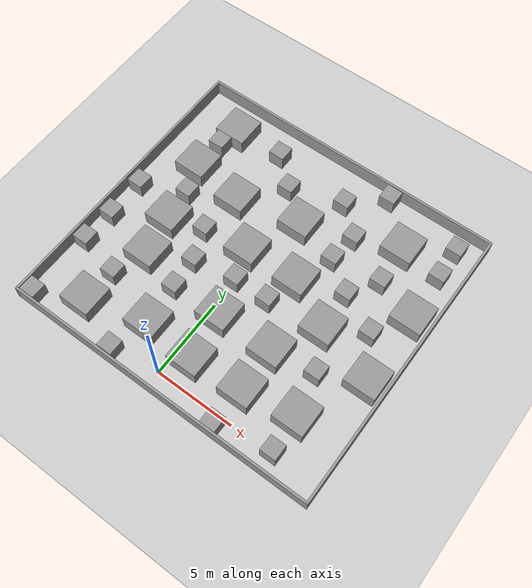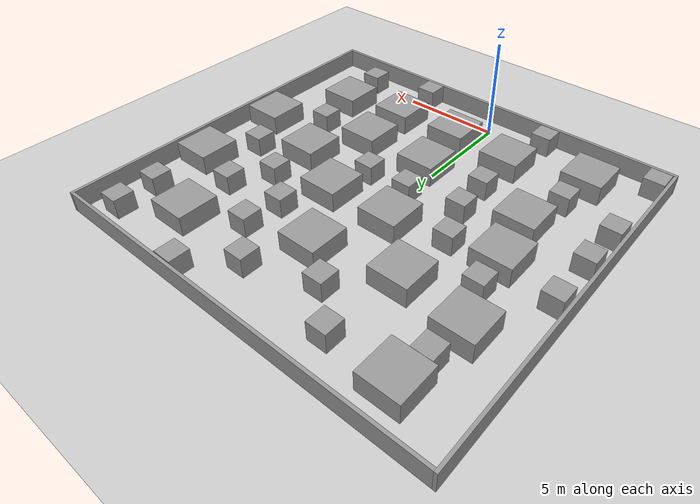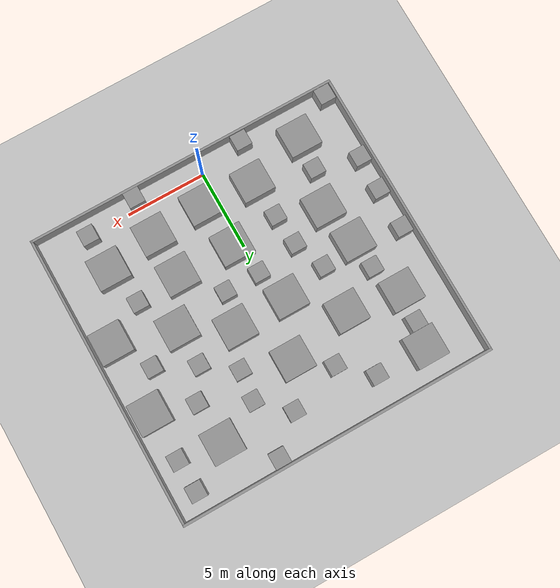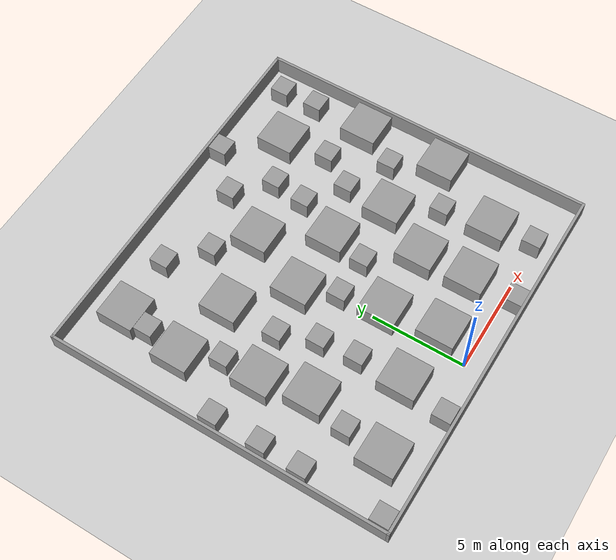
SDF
<sdf version="1.6">
 <world name="default">
  <light name="sun" type="directional">
   <pose>0 0 10 0 -0 0</pose>
   <diffuse>0.8 0.8 0.8 1</diffuse>
   <specular>0.2 0.2 0.2 1</specular>
   <attenuation>
    <range>1000</range>
    <constant>0.9</constant>
    <linear>0.01</linear>
    <quadratic>0.001</quadratic>
   </attenuation>
   <direction>-0.5 0.1 -0.9</direction>
  </light>
  <model name="ground_plane">
   <static>1</static>
   <link name="link">
    <collision name="collision">
     <geometry><plane><normal>0 0 1</normal><size>100 100</size></plane></geometry>
     <surface><friction><ode><mu>100</mu><mu2>50</mu2></ode></friction></surface>
    </collision>
    <visual name="visual">
     <cast_shadows>0</cast_shadows>
     <geometry><plane><normal>0 0 1</normal><size>100 100</size></plane></geometry>
     <material>
      <script><uri>file://media/materials/scripts/gazebo.material</uri><name>Gazebo/Grey</name></script>
     </material>
    </visual>
   </link>
  </model>
  <gravity>0 0 -9.8</gravity>
  <magnetic_field>6e-06 2.3e-05 -4.2e-05</magnetic_field>
  <atmosphere type="adiabatic"/>
  <physics name="default_physics" default="0" type="ode">
   <max_step_size>0.001</max_step_size>
   <real_time_factor>1</real_time_factor>
   <real_time_update_rate>1000</real_time_update_rate>
  </physics>
  <scene><ambient>0.4 0.4 0.4 1</ambient><background>0.7 0.7 0.7 1</background><shadows>1</shadows></scene>
  <spherical_coordinates>
   <surface_model>EARTH_WGS84</surface_model>
   <latitude_deg>0</latitude_deg>
   <longitude_deg>0</longitude_deg>
   <elevation>0</elevation>
   <heading_deg>0</heading_deg>
  </spherical_coordinates>
  <model name="map1">
   <pose>0.697678 8.0747 0 0 -0 0</pose>
   <link name="Wall_0">
    <collision name="Wall_0_Collision">
     <geometry><box><size>20 0.15 1</size></box></geometry>
     <pose>0 0 0.5 0 -0 0</pose>
    </collision>
    <visual name="Wall_0_Visual">
     <pose>0 0 0.5 0 -0 0</pose>
     <geometry><box><size>20 0.15 1</size></box></geometry>
     <material>
      <script><uri>file://media/materials/scripts/gazebo.material</uri><name>Gazebo/Grey</name></script>
      <ambient>1 1 1 1</ambient>
     </material>
     <meta><layer>0</layer></meta>
    </visual>
    <pose>0 9.175 0 0 -0 0</pose>
   </link>
   <link name="Wall_3">
    <collision name="Wall_3_Collision">
     <geometry><box><size>18.5 0.15 1</size></box></geometry>
     <pose>0 0 0.5 0 -0 0</pose>
    </collision>
    <visual name="Wall_3_Visual">
     <pose>0 0 0.5 0 -0 0</pose>
     <geometry><box><size>18.5 0.15 1</size></box></geometry>
     <material>
      <script><uri>file://media/materials/scripts/gazebo.material</uri><name>Gazebo/Grey</name></script>
      <ambient>1 1 1 1</ambient>
     </material>
     <meta><layer>0</layer></meta>
    </visual>
    <pose>9.925 0 0 0 -0 -1.5708</pose>
   </link>
   <link name="Wall_4">
    <collision name="Wall_4_Collision">
     <geometry><box><size>20 0.15 1</size></box></geometry>
     <pose>0 0 0.5 0 -0 0</pose>
    </collision>
    <visual name="Wall_4_Visual">
     <pose>0 0 0.5 0 -0 0</pose>
     <geometry><box><size>20 0.15 1</size></box></geometry>
     <material>
      <script><uri>file://media/materials/scripts/gazebo.material</uri><name>Gazebo/Grey</name></script>
      <ambient>1 1 1 1</ambient>
     </material>
     <meta><layer>0</layer></meta>
    </visual>
    <pose>0 -9.175 0 0 -0 3.14159</pose>
   </link>
   <link name="Wall_5">
    <collision name="Wall_5_Collision">
     <geometry><box><size>18.5 0.15 1</size></box></geometry>
     <pose>0 0 0.5 0 -0 0</pose>
    </collision>
    <visual name="Wall_5_Visual">
     <pose>0 0 0.5 0 -0 0</pose>
     <geometry><box><size>18.5 0.15 1</size></box></geometry>
     <material>
      <script><uri>file://media/materials/scripts/gazebo.material</uri><name>Gazebo/Grey</name></script>
      <ambient>1 1 1 1</ambient>
     </material>
     <meta><layer>0</layer></meta>
    </visual>
    <pose>-9.925 0 0 0 -0 1.5708</pose>
   </link>
   <static>1</static>
  </model>
  <model name="box3">
   <link name="link_0">
    <inertial>
     <mass>200</mass>
     <inertia><ixx>83.3333</ixx><ixy>0</ixy><ixz>0</ixz><iyy>83.3333</iyy><iyz>0</iyz><izz>133.333</izz></inertia>
     <pose>0 0 1 0 -0 0</pose>
    </inertial>
    <visual name="visual">
     <geometry><box><size>2 2 1</size></box></geometry>
     <material>
      <lighting>1</lighting>
      <script><uri>file://media/materials/scripts/gazebo.material</uri><name>Gazebo/Grey</name></script>
      <shader type="pixel"><normal_map>__default__</normal_map></shader>
      <ambient>0.3 0.3 0.3 1</ambient>
      <diffuse>0.7 0.7 0.7 1</diffuse>
      <specular>0.01 0.01 0.01 1</specular>
      <emissive>0 0 0 1</emissive>
     </material>
    </visual>
    <collision name="collision">
     <geometry><box><size>2 2 1</size></box></geometry>
     <surface>
      <friction>
       <ode><mu>1</mu><mu2>1</mu2><fdir1>0 0 0</fdir1><slip1>0</slip1><slip2>0</slip2></ode>
       <torsional>
        <coefficient>1</coefficient>
        <patch_radius>0</patch_radius>
        <surface_radius>0</surface_radius>
        <use_patch_radius>1</use_patch_radius>
        <ode><slip>0</slip></ode>
       </torsional>
      </friction>
      <bounce><restitution_coefficient>0</restitution_coefficient><threshold>1e+06</threshold></bounce>
      <contact>
       <collide_without_contact>0</collide_without_contact>
       <collide_without_contact_bitmask>1</collide_without_contact_bitmask>
       <collide_bitmask>1</collide_bitmask>
       <ode>
        <soft_cfm>0</soft_cfm>
        <soft_erp>0.2</soft_erp>
        <kp>1e+13</kp>
        <kd>1</kd>
        <max_vel>0.01</max_vel>
        <min_depth>0</min_depth>
       </ode>
       <bullet>
        <split_impulse>1</split_impulse>
        <split_impulse_penetration_threshold>-0.01</split_impulse_penetration_threshold>
        <soft_cfm>0</soft_cfm>
        <soft_erp>0.2</soft_erp>
        <kp>1e+13</kp>
        <kd>1</kd>
       </bullet>
      </contact>
     </surface>
    </collision>
   </link>
   <static>0</static>
   <pose>1.01568 1.72958 0.499999 -1e-06 -2e-06 4.8e-05</pose>
  </model>
  <model name="box3_clone">
   <link name="link_0">
    <inertial>
     <mass>200</mass>
     <inertia><ixx>83.3333</ixx><ixy>0</ixy><ixz>0</ixz><iyy>83.3333</iyy><iyz>0</iyz><izz>133.333</izz></inertia>
     <pose>0 0 1 0 -0 0</pose>
    </inertial>
    <visual name="visual">
     <geometry><box><size>2 2 1</size></box></geometry>
     <material>
      <lighting>1</lighting>
      <script><uri>file://media/materials/scripts/gazebo.material</uri><name>Gazebo/Grey</name></script>
      <shader type="pixel"><normal_map>__default__</normal_map></shader>
      <ambient>0.3 0.3 0.3 1</ambient>
      <diffuse>0.7 0.7 0.7 1</diffuse>
      <specular>0.01 0.01 0.01 1</specular>
      <emissive>0 0 0 1</emissive>
     </material>
    </visual>
    <collision name="collision">
     <geometry><box><size>2 2 1</size></box></geometry>
     <surface>
      <friction>
       <ode><mu>1</mu><mu2>1</mu2><fdir1>0 0 0</fdir1><slip1>0</slip1><slip2>0</slip2></ode>
       <torsional>
        <coefficient>1</coefficient>
        <patch_radius>0</patch_radius>
        <surface_radius>0</surface_radius>
        <use_patch_radius>1</use_patch_radius>
        <ode><slip>0</slip></ode>
       </torsional>
      </friction>
      <bounce><restitution_coefficient>0</restitution_coefficient><threshold>1e+06</threshold></bounce>
      <contact>
       <collide_without_contact>0</collide_without_contact>
       <collide_without_contact_bitmask>1</collide_without_contact_bitmask>
       <collide_bitmask>1</collide_bitmask>
       <ode>
        <soft_cfm>0</soft_cfm>
        <soft_erp>0.2</soft_erp>
        <kp>1e+13</kp>
        <kd>1</kd>
        <max_vel>0.01</max_vel>
        <min_depth>0</min_depth>
       </ode>
       <bullet>
        <split_impulse>1</split_impulse>
        <split_impulse_penetration_threshold>-0.01</split_impulse_penetration_threshold>
        <soft_cfm>0</soft_cfm>
        <soft_erp>0.2</soft_erp>
        <kp>1e+13</kp>
        <kd>1</kd>
       </bullet>
      </contact>
     </surface>
    </collision>
   </link>
   <static>0</static>
   <pose>4.28423 1.95795 0.499996 1e-06 3e-06 0.000328</pose>
  </model>
  <model name="box3_clone_0">
   <link name="link_0">
    <inertial>
     <mass>200</mass>
     <inertia><ixx>83.3333</ixx><ixy>0</ixy><ixz>0</ixz><iyy>83.3333</iyy><iyz>0</iyz><izz>133.333</izz></inertia>
     <pose>0 0 1 0 -0 0</pose>
    </inertial>
    <visual name="visual">
     <geometry><box><size>2 2 1</size></box></geometry>
     <material>
      <lighting>1</lighting>
      <script><uri>file://media/materials/scripts/gazebo.material</uri><name>Gazebo/Grey</name></script>
      <shader type="pixel"><normal_map>__default__</normal_map></shader>
      <ambient>0.3 0.3 0.3 1</ambient>
      <diffuse>0.7 0.7 0.7 1</diffuse>
      <specular>0.01 0.01 0.01 1</specular>
      <emissive>0 0 0 1</emissive>
     </material>
    </visual>
    <collision name="collision">
     <geometry><box><size>2 2 1</size></box></geometry>
     <surface>
      <friction>
       <ode><mu>1</mu><mu2>1</mu2><fdir1>0 0 0</fdir1><slip1>0</slip1><slip2>0</slip2></ode>
       <torsional>
        <coefficient>1</coefficient>
        <patch_radius>0</patch_radius>
        <surface_radius>0</surface_radius>
        <use_patch_radius>1</use_patch_radius>
        <ode><slip>0</slip></ode>
       </torsional>
      </friction>
      <bounce><restitution_coefficient>0</restitution_coefficient><threshold>1e+06</threshold></bounce>
      <contact>
       <collide_without_contact>0</collide_without_contact>
       <collide_without_contact_bitmask>1</collide_without_contact_bitmask>
       <collide_bitmask>1</collide_bitmask>
       <ode>
        <soft_cfm>0</soft_cfm>
        <soft_erp>0.2</soft_erp>
        <kp>1e+13</kp>
        <kd>1</kd>
        <max_vel>0.01</max_vel>
        <min_depth>0</min_depth>
       </ode>
       <bullet>
        <split_impulse>1</split_impulse>
        <split_impulse_penetration_threshold>-0.01</split_impulse_penetration_threshold>
        <soft_cfm>0</soft_cfm>
        <soft_erp>0.2</soft_erp>
        <kp>1e+13</kp>
        <kd>1</kd>
       </bullet>
      </contact>
     </surface>
    </collision>
   </link>
   <static>0</static>
   <pose>7.49997 2.45483 0.499996 3e-06 1e-06 0.00012</pose>
  </model>
  <model name="box3_clone_1">
   <link name="link_0">
    <inertial>
     <mass>200</mass>
     <inertia><ixx>83.3333</ixx><ixy>0</ixy><ixz>0</ixz><iyy>83.3333</iyy><iyz>0</iyz><izz>133.333</izz></inertia>
     <pose>0 0 1 0 -0 0</pose>
    </inertial>
    <visual name="visual">
     <geometry><box><size>2 2 1</size></box></geometry>
     <material>
      <lighting>1</lighting>
      <script><uri>file://media/materials/scripts/gazebo.material</uri><name>Gazebo/Grey</name></script>
      <shader type="pixel"><normal_map>__default__</normal_map></shader>
      <ambient>0.3 0.3 0.3 1</ambient>
      <diffuse>0.7 0.7 0.7 1</diffuse>
      <specular>0.01 0.01 0.01 1</specular>
      <emissive>0 0 0 1</emissive>
     </material>
    </visual>
    <collision name="collision">
     <geometry><box><size>2 2 1</size></box></geometry>
     <surface>
      <friction>
       <ode><mu>1</mu><mu2>1</mu2><fdir1>0 0 0</fdir1><slip1>0</slip1><slip2>0</slip2></ode>
       <torsional>
        <coefficient>1</coefficient>
        <patch_radius>0</patch_radius>
        <surface_radius>0</surface_radius>
        <use_patch_radius>1</use_patch_radius>
        <ode><slip>0</slip></ode>
       </torsional>
      </friction>
      <bounce><restitution_coefficient>0</restitution_coefficient><threshold>1e+06</threshold></bounce>
      <contact>
       <collide_without_contact>0</collide_without_contact>
       <collide_without_contact_bitmask>1</collide_without_contact_bitmask>
       <collide_bitmask>1</collide_bitmask>
       <ode>
        <soft_cfm>0</soft_cfm>
        <soft_erp>0.2</soft_erp>
        <kp>1e+13</kp>
        <kd>1</kd>
        <max_vel>0.01</max_vel>
        <min_depth>0</min_depth>
       </ode>
       <bullet>
        <split_impulse>1</split_impulse>
        <split_impulse_penetration_threshold>-0.01</split_impulse_penetration_threshold>
        <soft_cfm>0</soft_cfm>
        <soft_erp>0.2</soft_erp>
        <kp>1e+13</kp>
        <kd>1</kd>
       </bullet>
      </contact>
     </surface>
    </collision>
   </link>
   <static>0</static>
   <pose>4.18679 4.69973 0.499996 -1e-06 -3e-06 0.00033</pose>
  </model>
  <model name="box3_clone_2">
   <link name="link_0">
    <inertial>
     <mass>200</mass>
     <inertia><ixx>83.3333</ixx><ixy>0</ixy><ixz>0</ixz><iyy>83.3333</iyy><iyz>0</iyz><izz>133.333</izz></inertia>
     <pose>0 0 1 0 -0 0</pose>
    </inertial>
    <visual name="visual">
     <geometry><box><size>2 2 1</size></box></geometry>
     <material>
      <lighting>1</lighting>
      <script><uri>file://media/materials/scripts/gazebo.material</uri><name>Gazebo/Grey</name></script>
      <shader type="pixel"><normal_map>__default__</normal_map></shader>
      <ambient>0.3 0.3 0.3 1</ambient>
      <diffuse>0.7 0.7 0.7 1</diffuse>
      <specular>0.01 0.01 0.01 1</specular>
      <emissive>0 0 0 1</emissive>
     </material>
    </visual>
    <collision name="collision">
     <geometry><box><size>2 2 1</size></box></geometry>
     <surface>
      <friction>
       <ode><mu>1</mu><mu2>1</mu2><fdir1>0 0 0</fdir1><slip1>0</slip1><slip2>0</slip2></ode>
       <torsional>
        <coefficient>1</coefficient>
        <patch_radius>0</patch_radius>
        <surface_radius>0</surface_radius>
        <use_patch_radius>1</use_patch_radius>
        <ode><slip>0</slip></ode>
       </torsional>
      </friction>
      <bounce><restitution_coefficient>0</restitution_coefficient><threshold>1e+06</threshold></bounce>
      <contact>
       <collide_without_contact>0</collide_without_contact>
       <collide_without_contact_bitmask>1</collide_without_contact_bitmask>
       <collide_bitmask>1</collide_bitmask>
       <ode>
        <soft_cfm>0</soft_cfm>
        <soft_erp>0.2</soft_erp>
        <kp>1e+13</kp>
        <kd>1</kd>
        <max_vel>0.01</max_vel>
        <min_depth>0</min_depth>
       </ode>
       <bullet>
        <split_impulse>1</split_impulse>
        <split_impulse_penetration_threshold>-0.01</split_impulse_penetration_threshold>
        <soft_cfm>0</soft_cfm>
        <soft_erp>0.2</soft_erp>
        <kp>1e+13</kp>
        <kd>1</kd>
       </bullet>
      </contact>
     </surface>
    </collision>
   </link>
   <static>0</static>
   <pose>0.599355 4.71049 0.499996 -3e-06 1e-06 0.000372</pose>
  </model>
  <model name="box3_clone_2_clone">
   <link name="link_0">
    <inertial>
     <mass>200</mass>
     <inertia><ixx>83.3333</ixx><ixy>0</ixy><ixz>0</ixz><iyy>83.3333</iyy><iyz>0</iyz><izz>133.333</izz></inertia>
     <pose>0 0 1 0 -0 0</pose>
    </inertial>
    <visual name="visual">
     <geometry><box><size>2 2 1</size></box></geometry>
     <material>
      <lighting>1</lighting>
      <script><uri>file://media/materials/scripts/gazebo.material</uri><name>Gazebo/Grey</name></script>
      <shader type="pixel"><normal_map>__default__</normal_map></shader>
      <ambient>0.3 0.3 0.3 1</ambient>
      <diffuse>0.7 0.7 0.7 1</diffuse>
      <specular>0.01 0.01 0.01 1</specular>
      <emissive>0 0 0 1</emissive>
     </material>
    </visual>
    <collision name="collision">
     <geometry><box><size>2 2 1</size></box></geometry>
     <surface>
      <friction>
       <ode><mu>1</mu><mu2>1</mu2><fdir1>0 0 0</fdir1><slip1>0</slip1><slip2>0</slip2></ode>
       <torsional>
        <coefficient>1</coefficient>
        <patch_radius>0</patch_radius>
        <surface_radius>0</surface_radius>
        <use_patch_radius>1</use_patch_radius>
        <ode><slip>0</slip></ode>
       </torsional>
      </friction>
      <bounce><restitution_coefficient>0</restitution_coefficient><threshold>1e+06</threshold></bounce>
      <contact>
       <collide_without_contact>0</collide_without_contact>
       <collide_without_contact_bitmask>1</collide_without_contact_bitmask>
       <collide_bitmask>1</collide_bitmask>
       <ode>
        <soft_cfm>0</soft_cfm>
        <soft_erp>0.2</soft_erp>
        <kp>1e+13</kp>
        <kd>1</kd>
        <max_vel>0.01</max_vel>
        <min_depth>0</min_depth>
       </ode>
       <bullet>
        <split_impulse>1</split_impulse>
        <split_impulse_penetration_threshold>-0.01</split_impulse_penetration_threshold>
        <soft_cfm>0</soft_cfm>
        <soft_erp>0.2</soft_erp>
        <kp>1e+13</kp>
        <kd>1</kd>
       </bullet>
      </contact>
     </surface>
    </collision>
   </link>
   <static>0</static>
   <pose>-2.2638 1.99782 0.499996 1e-06 3e-06 0.000332</pose>
  </model>
  <model name="box3_clone_2_clone_0">
   <link name="link_0">
    <inertial>
     <mass>200</mass>
     <inertia><ixx>83.3333</ixx><ixy>0</ixy><ixz>0</ixz><iyy>83.3333</iyy><iyz>0</iyz><izz>133.333</izz></inertia>
     <pose>0 0 1 0 -0 0</pose>
    </inertial>
    <visual name="visual">
     <geometry><box><size>2 2 1</size></box></geometry>
     <material>
      <lighting>1</lighting>
      <script><uri>file://media/materials/scripts/gazebo.material</uri><name>Gazebo/Grey</name></script>
      <shader type="pixel"><normal_map>__default__</normal_map></shader>
      <ambient>0.3 0.3 0.3 1</ambient>
      <diffuse>0.7 0.7 0.7 1</diffuse>
      <specular>0.01 0.01 0.01 1</specular>
      <emissive>0 0 0 1</emissive>
     </material>
    </visual>
    <collision name="collision">
     <geometry><box><size>2 2 1</size></box></geometry>
     <surface>
      <friction>
       <ode><mu>1</mu><mu2>1</mu2><fdir1>0 0 0</fdir1><slip1>0</slip1><slip2>0</slip2></ode>
       <torsional>
        <coefficient>1</coefficient>
        <patch_radius>0</patch_radius>
        <surface_radius>0</surface_radius>
        <use_patch_radius>1</use_patch_radius>
        <ode><slip>0</slip></ode>
       </torsional>
      </friction>
      <bounce><restitution_coefficient>0</restitution_coefficient><threshold>1e+06</threshold></bounce>
      <contact>
       <collide_without_contact>0</collide_without_contact>
       <collide_without_contact_bitmask>1</collide_without_contact_bitmask>
       <collide_bitmask>1</collide_bitmask>
       <ode>
        <soft_cfm>0</soft_cfm>
        <soft_erp>0.2</soft_erp>
        <kp>1e+13</kp>
        <kd>1</kd>
        <max_vel>0.01</max_vel>
        <min_depth>0</min_depth>
       </ode>
       <bullet>
        <split_impulse>1</split_impulse>
        <split_impulse_penetration_threshold>-0.01</split_impulse_penetration_threshold>
        <soft_cfm>0</soft_cfm>
        <soft_erp>0.2</soft_erp>
        <kp>1e+13</kp>
        <kd>1</kd>
       </bullet>
      </contact>
     </surface>
    </collision>
   </link>
   <static>0</static>
   <pose>-5.14191 5.33349 0.499996 3e-06 1e-06 0.000124</pose>
  </model>
  <model name="box">
   <link name="link_3">
    <inertial>
     <mass>1</mass>
     <inertia>
      <ixx>0.166667</ixx>
      <ixy>0</ixy>
      <ixz>0</ixz>
      <iyy>0.166667</iyy>
      <iyz>0</iyz>
      <izz>0.166667</izz>
     </inertia>
    </inertial>
    <pose>-0.10623 1.19174 0.5 0 -0 0</pose>
    <visual name="visual">
     <geometry><box><size>1 1 1</size></box></geometry>
     <material>
      <lighting>1</lighting>
      <script><uri>file://media/materials/scripts/gazebo.material</uri><name>Gazebo/Grey</name></script>
      <shader type="pixel"/>
     </material>
    </visual>
    <collision name="collision">
     <geometry><box><size>1 1 1</size></box></geometry>
     <surface>
      <friction>
       <ode><mu>1</mu><mu2>1</mu2><fdir1>0 0 0</fdir1><slip1>0</slip1><slip2>0</slip2></ode>
       <torsional>
        <coefficient>1</coefficient>
        <patch_radius>0</patch_radius>
        <surface_radius>0</surface_radius>
        <use_patch_radius>1</use_patch_radius>
        <ode><slip>0</slip></ode>
       </torsional>
      </friction>
      <bounce><restitution_coefficient>0</restitution_coefficient><threshold>1e+06</threshold></bounce>
      <contact>
       <collide_without_contact>0</collide_without_contact>
       <collide_without_contact_bitmask>1</collide_without_contact_bitmask>
       <collide_bitmask>1</collide_bitmask>
       <ode>
        <soft_cfm>0</soft_cfm>
        <soft_erp>0.2</soft_erp>
        <kp>1e+13</kp>
        <kd>1</kd>
        <max_vel>0.01</max_vel>
        <min_depth>0</min_depth>
       </ode>
       <bullet>
        <split_impulse>1</split_impulse>
        <split_impulse_penetration_threshold>-0.01</split_impulse_penetration_threshold>
        <soft_cfm>0</soft_cfm>
        <soft_erp>0.2</soft_erp>
        <kp>1e+13</kp>
        <kd>1</kd>
       </bullet>
      </contact>
     </surface>
    </collision>
   </link>
   <static>0</static>
   <pose>-2.34355 3.25149 0 0 -0 0</pose>
  </model>
  <model name="box3_clone_2_clone_1">
   <link name="link_0">
    <inertial>
     <mass>200</mass>
     <inertia><ixx>83.3333</ixx><ixy>0</ixy><ixz>0</ixz><iyy>83.3333</iyy><iyz>0</iyz><izz>133.333</izz></inertia>
     <pose>0 0 1 0 -0 0</pose>
    </inertial>
    <visual name="visual">
     <geometry><box><size>2 2 1</size></box></geometry>
     <material>
      <lighting>1</lighting>
      <script><uri>file://media/materials/scripts/gazebo.material</uri><name>Gazebo/Grey</name></script>
      <shader type="pixel"><normal_map>__default__</normal_map></shader>
      <ambient>0.3 0.3 0.3 1</ambient>
      <diffuse>0.7 0.7 0.7 1</diffuse>
      <specular>0.01 0.01 0.01 1</specular>
      <emissive>0 0 0 1</emissive>
     </material>
    </visual>
    <collision name="collision">
     <geometry><box><size>2 2 1</size></box></geometry>
     <surface>
      <friction>
       <ode><mu>1</mu><mu2>1</mu2><fdir1>0 0 0</fdir1><slip1>0</slip1><slip2>0</slip2></ode>
       <torsional>
        <coefficient>1</coefficient>
        <patch_radius>0</patch_radius>
        <surface_radius>0</surface_radius>
        <use_patch_radius>1</use_patch_radius>
        <ode><slip>0</slip></ode>
       </torsional>
      </friction>
      <bounce><restitution_coefficient>0</restitution_coefficient><threshold>1e+06</threshold></bounce>
      <contact>
       <collide_without_contact>0</collide_without_contact>
       <collide_without_contact_bitmask>1</collide_without_contact_bitmask>
       <collide_bitmask>1</collide_bitmask>
       <ode>
        <soft_cfm>0</soft_cfm>
        <soft_erp>0.2</soft_erp>
        <kp>1e+13</kp>
        <kd>1</kd>
        <max_vel>0.01</max_vel>
        <min_depth>0</min_depth>
       </ode>
       <bullet>
        <split_impulse>1</split_impulse>
        <split_impulse_penetration_threshold>-0.01</split_impulse_penetration_threshold>
        <soft_cfm>0</soft_cfm>
        <soft_erp>0.2</soft_erp>
        <kp>1e+13</kp>
        <kd>1</kd>
       </bullet>
      </contact>
     </surface>
    </collision>
   </link>
   <static>0</static>
   <pose>-6.01509 0.963971 0.5 0 -0 0.00035</pose>
  </model>
  <model name="box_clone">
   <link name="link_3">
    <inertial>
     <mass>1</mass>
     <inertia>
      <ixx>0.166667</ixx>
      <ixy>0</ixy>
      <ixz>0</ixz>
      <iyy>0.166667</iyy>
      <iyz>0</iyz>
      <izz>0.166667</izz>
     </inertia>
    </inertial>
    <pose>-0.10623 1.19174 0.5 0 -0 0</pose>
    <visual name="visual">
     <geometry><box><size>1 1 1</size></box></geometry>
     <material>
      <lighting>1</lighting>
      <script><uri>file://media/materials/scripts/gazebo.material</uri><name>Gazebo/Grey</name></script>
      <shader type="pixel"/>
     </material>
    </visual>
    <collision name="collision">
     <geometry><box><size>1 1 1</size></box></geometry>
     <surface>
      <friction>
       <ode><mu>1</mu><mu2>1</mu2><fdir1>0 0 0</fdir1><slip1>0</slip1><slip2>0</slip2></ode>
       <torsional>
        <coefficient>1</coefficient>
        <patch_radius>0</patch_radius>
        <surface_radius>0</surface_radius>
        <use_patch_radius>1</use_patch_radius>
        <ode><slip>0</slip></ode>
       </torsional>
      </friction>
      <bounce><restitution_coefficient>0</restitution_coefficient><threshold>1e+06</threshold></bounce>
      <contact>
       <collide_without_contact>0</collide_without_contact>
       <collide_without_contact_bitmask>1</collide_without_contact_bitmask>
       <collide_bitmask>1</collide_bitmask>
       <ode>
        <soft_cfm>0</soft_cfm>
        <soft_erp>0.2</soft_erp>
        <kp>1e+13</kp>
        <kd>1</kd>
        <max_vel>0.01</max_vel>
        <min_depth>0</min_depth>
       </ode>
       <bullet>
        <split_impulse>1</split_impulse>
        <split_impulse_penetration_threshold>-0.01</split_impulse_penetration_threshold>
        <soft_cfm>0</soft_cfm>
        <soft_erp>0.2</soft_erp>
        <kp>1e+13</kp>
        <kd>1</kd>
       </bullet>
      </contact>
     </surface>
    </collision>
   </link>
   <static>0</static>
   <pose>-5.7246 1.90952 0 0 -0 0</pose>
  </model>
  <model name="box_clone_0">
   <link name="link_3">
    <inertial>
     <mass>1</mass>
     <inertia>
      <ixx>0.166667</ixx>
      <ixy>0</ixy>
      <ixz>0</ixz>
      <iyy>0.166667</iyy>
      <iyz>0</iyz>
      <izz>0.166667</izz>
     </inertia>
    </inertial>
    <pose>-0.10623 1.19174 0.5 0 -0 0</pose>
    <visual name="visual">
     <geometry><box><size>1 1 1</size></box></geometry>
     <material>
      <lighting>1</lighting>
      <script><uri>file://media/materials/scripts/gazebo.material</uri><name>Gazebo/Grey</name></script>
      <shader type="pixel"/>
     </material>
    </visual>
    <collision name="collision">
     <geometry><box><size>1 1 1</size></box></geometry>
     <surface>
      <friction>
       <ode><mu>1</mu><mu2>1</mu2><fdir1>0 0 0</fdir1><slip1>0</slip1><slip2>0</slip2></ode>
       <torsional>
        <coefficient>1</coefficient>
        <patch_radius>0</patch_radius>
        <surface_radius>0</surface_radius>
        <use_patch_radius>1</use_patch_radius>
        <ode><slip>0</slip></ode>
       </torsional>
      </friction>
      <bounce><restitution_coefficient>0</restitution_coefficient><threshold>1e+06</threshold></bounce>
      <contact>
       <collide_without_contact>0</collide_without_contact>
       <collide_without_contact_bitmask>1</collide_without_contact_bitmask>
       <collide_bitmask>1</collide_bitmask>
       <ode>
        <soft_cfm>0</soft_cfm>
        <soft_erp>0.2</soft_erp>
        <kp>1e+13</kp>
        <kd>1</kd>
        <max_vel>0.01</max_vel>
        <min_depth>0</min_depth>
       </ode>
       <bullet>
        <split_impulse>1</split_impulse>
        <split_impulse_penetration_threshold>-0.01</split_impulse_penetration_threshold>
        <soft_cfm>0</soft_cfm>
        <soft_erp>0.2</soft_erp>
        <kp>1e+13</kp>
        <kd>1</kd>
       </bullet>
      </contact>
     </surface>
    </collision>
   </link>
   <static>0</static>
   <pose>-8.4247 2.60163 0 0 -0 0</pose>
  </model>
  <model name="box_clone_1">
   <link name="link_3">
    <inertial>
     <mass>1</mass>
     <inertia>
      <ixx>0.166667</ixx>
      <ixy>0</ixy>
      <ixz>0</ixz>
      <iyy>0.166667</iyy>
      <iyz>0</iyz>
      <izz>0.166667</izz>
     </inertia>
    </inertial>
    <pose>-0.10623 1.19174 0.5 0 -0 0</pose>
    <visual name="visual">
     <geometry><box><size>1 1 1</size></box></geometry>
     <material>
      <lighting>1</lighting>
      <script><uri>file://media/materials/scripts/gazebo.material</uri><name>Gazebo/Grey</name></script>
      <shader type="pixel"/>
     </material>
    </visual>
    <collision name="collision">
     <geometry><box><size>1 1 1</size></box></geometry>
     <surface>
      <friction>
       <ode><mu>1</mu><mu2>1</mu2><fdir1>0 0 0</fdir1><slip1>0</slip1><slip2>0</slip2></ode>
       <torsional>
        <coefficient>1</coefficient>
        <patch_radius>0</patch_radius>
        <surface_radius>0</surface_radius>
        <use_patch_radius>1</use_patch_radius>
        <ode><slip>0</slip></ode>
       </torsional>
      </friction>
      <bounce><restitution_coefficient>0</restitution_coefficient><threshold>1e+06</threshold></bounce>
      <contact>
       <collide_without_contact>0</collide_without_contact>
       <collide_without_contact_bitmask>1</collide_without_contact_bitmask>
       <collide_bitmask>1</collide_bitmask>
       <ode>
        <soft_cfm>0</soft_cfm>
        <soft_erp>0.2</soft_erp>
        <kp>1e+13</kp>
        <kd>1</kd>
        <max_vel>0.01</max_vel>
        <min_depth>0</min_depth>
       </ode>
       <bullet>
        <split_impulse>1</split_impulse>
        <split_impulse_penetration_threshold>-0.01</split_impulse_penetration_threshold>
        <soft_cfm>0</soft_cfm>
        <soft_erp>0.2</soft_erp>
        <kp>1e+13</kp>
        <kd>1</kd>
       </bullet>
      </contact>
     </surface>
    </collision>
   </link>
   <static>0</static>
   <pose>2.36939 5.72598 0 0 -0 0</pose>
  </model>
  <model name="box_clone_2">
   <link name="link_3">
    <inertial>
     <mass>1</mass>
     <inertia>
      <ixx>0.166667</ixx>
      <ixy>0</ixy>
      <ixz>0</ixz>
      <iyy>0.166667</iyy>
      <iyz>0</iyz>
      <izz>0.166667</izz>
     </inertia>
    </inertial>
    <pose>-0.10623 1.19174 0.5 0 -0 0</pose>
    <visual name="visual">
     <geometry><box><size>1 1 1</size></box></geometry>
     <material>
      <lighting>1</lighting>
      <script><uri>file://media/materials/scripts/gazebo.material</uri><name>Gazebo/Grey</name></script>
      <shader type="pixel"/>
     </material>
    </visual>
    <collision name="collision">
     <geometry><box><size>1 1 1</size></box></geometry>
     <surface>
      <friction>
       <ode><mu>1</mu><mu2>1</mu2><fdir1>0 0 0</fdir1><slip1>0</slip1><slip2>0</slip2></ode>
       <torsional>
        <coefficient>1</coefficient>
        <patch_radius>0</patch_radius>
        <surface_radius>0</surface_radius>
        <use_patch_radius>1</use_patch_radius>
        <ode><slip>0</slip></ode>
       </torsional>
      </friction>
      <bounce><restitution_coefficient>0</restitution_coefficient><threshold>1e+06</threshold></bounce>
      <contact>
       <collide_without_contact>0</collide_without_contact>
       <collide_without_contact_bitmask>1</collide_without_contact_bitmask>
       <collide_bitmask>1</collide_bitmask>
       <ode>
        <soft_cfm>0</soft_cfm>
        <soft_erp>0.2</soft_erp>
        <kp>1e+13</kp>
        <kd>1</kd>
        <max_vel>0.01</max_vel>
        <min_depth>0</min_depth>
       </ode>
       <bullet>
        <split_impulse>1</split_impulse>
        <split_impulse_penetration_threshold>-0.01</split_impulse_penetration_threshold>
        <soft_cfm>0</soft_cfm>
        <soft_erp>0.2</soft_erp>
        <kp>1e+13</kp>
        <kd>1</kd>
       </bullet>
      </contact>
     </surface>
    </collision>
   </link>
   <static>0</static>
   <pose>0.150156 5.70574 0 0 -0 0</pose>
  </model>
  <model name="box_clone_3">
   <link name="link_3">
    <inertial>
     <mass>1</mass>
     <inertia>
      <ixx>0.166667</ixx>
      <ixy>0</ixy>
      <ixz>0</ixz>
      <iyy>0.166667</iyy>
      <iyz>0</iyz>
      <izz>0.166667</izz>
     </inertia>
    </inertial>
    <pose>-0.10623 1.19174 0.5 0 -0 0</pose>
    <visual name="visual">
     <geometry><box><size>1 1 1</size></box></geometry>
     <material>
      <lighting>1</lighting>
      <script><uri>file://media/materials/scripts/gazebo.material</uri><name>Gazebo/Grey</name></script>
      <shader type="pixel"/>
     </material>
    </visual>
    <collision name="collision">
     <geometry><box><size>1 1 1</size></box></geometry>
     <surface>
      <friction>
       <ode><mu>1</mu><mu2>1</mu2><fdir1>0 0 0</fdir1><slip1>0</slip1><slip2>0</slip2></ode>
       <torsional>
        <coefficient>1</coefficient>
        <patch_radius>0</patch_radius>
        <surface_radius>0</surface_radius>
        <use_patch_radius>1</use_patch_radius>
        <ode><slip>0</slip></ode>
       </torsional>
      </friction>
      <bounce><restitution_coefficient>0</restitution_coefficient><threshold>1e+06</threshold></bounce>
      <contact>
       <collide_without_contact>0</collide_without_contact>
       <collide_without_contact_bitmask>1</collide_without_contact_bitmask>
       <collide_bitmask>1</collide_bitmask>
       <ode>
        <soft_cfm>0</soft_cfm>
        <soft_erp>0.2</soft_erp>
        <kp>1e+13</kp>
        <kd>1</kd>
        <max_vel>0.01</max_vel>
        <min_depth>0</min_depth>
       </ode>
       <bullet>
        <split_impulse>1</split_impulse>
        <split_impulse_penetration_threshold>-0.01</split_impulse_penetration_threshold>
        <soft_cfm>0</soft_cfm>
        <soft_erp>0.2</soft_erp>
        <kp>1e+13</kp>
        <kd>1</kd>
       </bullet>
      </contact>
     </surface>
    </collision>
   </link>
   <static>0</static>
   <pose>-3.28539 7.2289 0 0 -0 0</pose>
  </model>
  <model name="box3_clone_2_clone_0_clone">
   <link name="link_0">
    <inertial>
     <mass>200</mass>
     <inertia><ixx>83.3333</ixx><ixy>0</ixy><ixz>0</ixz><iyy>83.3333</iyy><iyz>0</iyz><izz>133.333</izz></inertia>
     <pose>0 0 1 0 -0 0</pose>
    </inertial>
    <visual name="visual">
     <geometry><box><size>2 2 1</size></box></geometry>
     <material>
      <lighting>1</lighting>
      <script><uri>file://media/materials/scripts/gazebo.material</uri><name>Gazebo/Grey</name></script>
      <shader type="pixel"><normal_map>__default__</normal_map></shader>
      <ambient>0.3 0.3 0.3 1</ambient>
      <diffuse>0.7 0.7 0.7 1</diffuse>
      <specular>0.01 0.01 0.01 1</specular>
      <emissive>0 0 0 1</emissive>
     </material>
    </visual>
    <collision name="collision">
     <geometry><box><size>2 2 1</size></box></geometry>
     <surface>
      <friction>
       <ode><mu>1</mu><mu2>1</mu2><fdir1>0 0 0</fdir1><slip1>0</slip1><slip2>0</slip2></ode>
       <torsional>
        <coefficient>1</coefficient>
        <patch_radius>0</patch_radius>
        <surface_radius>0</surface_radius>
        <use_patch_radius>1</use_patch_radius>
        <ode><slip>0</slip></ode>
       </torsional>
      </friction>
      <bounce><restitution_coefficient>0</restitution_coefficient><threshold>1e+06</threshold></bounce>
      <contact>
       <collide_without_contact>0</collide_without_contact>
       <collide_without_contact_bitmask>1</collide_without_contact_bitmask>
       <collide_bitmask>1</collide_bitmask>
       <ode>
        <soft_cfm>0</soft_cfm>
        <soft_erp>0.2</soft_erp>
        <kp>1e+13</kp>
        <kd>1</kd>
        <max_vel>0.01</max_vel>
        <min_depth>0</min_depth>
       </ode>
       <bullet>
        <split_impulse>1</split_impulse>
        <split_impulse_penetration_threshold>-0.01</split_impulse_penetration_threshold>
        <soft_cfm>0</soft_cfm>
        <soft_erp>0.2</soft_erp>
        <kp>1e+13</kp>
        <kd>1</kd>
       </bullet>
      </contact>
     </surface>
    </collision>
   </link>
   <static>0</static>
   <pose>-5.6582 7.91578 0.499996 -1e-06 3e-06 0.000488</pose>
  </model>
  <model name="box3_clone_2_clone_0_clone_0">
   <link name="link_0">
    <inertial>
     <mass>200</mass>
     <inertia><ixx>83.3333</ixx><ixy>0</ixy><ixz>0</ixz><iyy>83.3333</iyy><iyz>0</iyz><izz>133.333</izz></inertia>
     <pose>0 0 1 0 -0 0</pose>
    </inertial>
    <visual name="visual">
     <geometry><box><size>2 2 1</size></box></geometry>
     <material>
      <lighting>1</lighting>
      <script><uri>file://media/materials/scripts/gazebo.material</uri><name>Gazebo/Grey</name></script>
      <shader type="pixel"><normal_map>__default__</normal_map></shader>
      <ambient>0.3 0.3 0.3 1</ambient>
      <diffuse>0.7 0.7 0.7 1</diffuse>
      <specular>0.01 0.01 0.01 1</specular>
      <emissive>0 0 0 1</emissive>
     </material>
    </visual>
    <collision name="collision">
     <geometry><box><size>2 2 1</size></box></geometry>
     <surface>
      <friction>
       <ode><mu>1</mu><mu2>1</mu2><fdir1>0 0 0</fdir1><slip1>0</slip1><slip2>0</slip2></ode>
       <torsional>
        <coefficient>1</coefficient>
        <patch_radius>0</patch_radius>
        <surface_radius>0</surface_radius>
        <use_patch_radius>1</use_patch_radius>
        <ode><slip>0</slip></ode>
       </torsional>
      </friction>
      <bounce><restitution_coefficient>0</restitution_coefficient><threshold>1e+06</threshold></bounce>
      <contact>
       <collide_without_contact>0</collide_without_contact>
       <collide_without_contact_bitmask>1</collide_without_contact_bitmask>
       <collide_bitmask>1</collide_bitmask>
       <ode>
        <soft_cfm>0</soft_cfm>
        <soft_erp>0.2</soft_erp>
        <kp>1e+13</kp>
        <kd>1</kd>
        <max_vel>0.01</max_vel>
        <min_depth>0</min_depth>
       </ode>
       <bullet>
        <split_impulse>1</split_impulse>
        <split_impulse_penetration_threshold>-0.01</split_impulse_penetration_threshold>
        <soft_cfm>0</soft_cfm>
        <soft_erp>0.2</soft_erp>
        <kp>1e+13</kp>
        <kd>1</kd>
       </bullet>
      </contact>
     </surface>
    </collision>
   </link>
   <static>0</static>
   <pose>-0.621552 8.90426 0.5 0 -0 0.000648</pose>
  </model>
  <model name="box_clone_2_clone">
   <link name="link_3">
    <inertial>
     <mass>1</mass>
     <inertia>
      <ixx>0.166667</ixx>
      <ixy>0</ixy>
      <ixz>0</ixz>
      <iyy>0.166667</iyy>
      <iyz>0</iyz>
      <izz>0.166667</izz>
     </inertia>
    </inertial>
    <pose>-0.10623 1.19174 0.5 0 -0 0</pose>
    <visual name="visual">
     <geometry><box><size>1 1 1</size></box></geometry>
     <material>
      <lighting>1</lighting>
      <script><uri>file://media/materials/scripts/gazebo.material</uri><name>Gazebo/Grey</name></script>
      <shader type="pixel"/>
     </material>
    </visual>
    <collision name="collision">
     <geometry><box><size>1 1 1</size></box></geometry>
     <surface>
      <friction>
       <ode><mu>1</mu><mu2>1</mu2><fdir1>0 0 0</fdir1><slip1>0</slip1><slip2>0</slip2></ode>
       <torsional>
        <coefficient>1</coefficient>
        <patch_radius>0</patch_radius>
        <surface_radius>0</surface_radius>
        <use_patch_radius>1</use_patch_radius>
        <ode><slip>0</slip></ode>
       </torsional>
      </friction>
      <bounce><restitution_coefficient>0</restitution_coefficient><threshold>1e+06</threshold></bounce>
      <contact>
       <collide_without_contact>0</collide_without_contact>
       <collide_without_contact_bitmask>1</collide_without_contact_bitmask>
       <collide_bitmask>1</collide_bitmask>
       <ode>
        <soft_cfm>0</soft_cfm>
        <soft_erp>0.2</soft_erp>
        <kp>1e+13</kp>
        <kd>1</kd>
        <max_vel>0.01</max_vel>
        <min_depth>0</min_depth>
       </ode>
       <bullet>
        <split_impulse>1</split_impulse>
        <split_impulse_penetration_threshold>-0.01</split_impulse_penetration_threshold>
        <soft_cfm>0</soft_cfm>
        <soft_erp>0.2</soft_erp>
        <kp>1e+13</kp>
        <kd>1</kd>
       </bullet>
      </contact>
     </surface>
    </collision>
   </link>
   <static>0</static>
   <pose>-2.51248 5.24742 0 0 -0 0</pose>
  </model>
  <model name="box3_clone_1_clone">
   <link name="link_0">
    <inertial>
     <mass>200</mass>
     <inertia><ixx>83.3333</ixx><ixy>0</ixy><ixz>0</ixz><iyy>83.3333</iyy><iyz>0</iyz><izz>133.333</izz></inertia>
     <pose>0 0 1 0 -0 0</pose>
    </inertial>
    <visual name="visual">
     <geometry><box><size>2 2 1</size></box></geometry>
     <material>
      <lighting>1</lighting>
      <script><uri>file://media/materials/scripts/gazebo.material</uri><name>Gazebo/Grey</name></script>
      <shader type="pixel"><normal_map>__default__</normal_map></shader>
      <ambient>0.3 0.3 0.3 1</ambient>
      <diffuse>0.7 0.7 0.7 1</diffuse>
      <specular>0.01 0.01 0.01 1</specular>
      <emissive>0 0 0 1</emissive>
     </material>
    </visual>
    <collision name="collision">
     <geometry><box><size>2 2 1</size></box></geometry>
     <surface>
      <friction>
       <ode><mu>1</mu><mu2>1</mu2><fdir1>0 0 0</fdir1><slip1>0</slip1><slip2>0</slip2></ode>
       <torsional>
        <coefficient>1</coefficient>
        <patch_radius>0</patch_radius>
        <surface_radius>0</surface_radius>
        <use_patch_radius>1</use_patch_radius>
        <ode><slip>0</slip></ode>
       </torsional>
      </friction>
      <bounce><restitution_coefficient>0</restitution_coefficient><threshold>1e+06</threshold></bounce>
      <contact>
       <collide_without_contact>0</collide_without_contact>
       <collide_without_contact_bitmask>1</collide_without_contact_bitmask>
       <collide_bitmask>1</collide_bitmask>
       <ode>
        <soft_cfm>0</soft_cfm>
        <soft_erp>0.2</soft_erp>
        <kp>1e+13</kp>
        <kd>1</kd>
        <max_vel>0.01</max_vel>
        <min_depth>0</min_depth>
       </ode>
       <bullet>
        <split_impulse>1</split_impulse>
        <split_impulse_penetration_threshold>-0.01</split_impulse_penetration_threshold>
        <soft_cfm>0</soft_cfm>
        <soft_erp>0.2</soft_erp>
        <kp>1e+13</kp>
        <kd>1</kd>
       </bullet>
      </contact>
     </surface>
    </collision>
   </link>
   <static>0</static>
   <pose>2.77209 8.98695 0.499996 3e-06 1e-06 0.000347</pose>
  </model>
  <model name="box3_clone_1_clone_0">
   <link name="link_0">
    <inertial>
     <mass>200</mass>
     <inertia><ixx>83.3333</ixx><ixy>0</ixy><ixz>0</ixz><iyy>83.3333</iyy><iyz>0</iyz><izz>133.333</izz></inertia>
     <pose>0 0 1 0 -0 0</pose>
    </inertial>
    <visual name="visual">
     <geometry><box><size>2 2 1</size></box></geometry>
     <material>
      <lighting>1</lighting>
      <script><uri>file://media/materials/scripts/gazebo.material</uri><name>Gazebo/Grey</name></script>
      <shader type="pixel"><normal_map>__default__</normal_map></shader>
      <ambient>0.3 0.3 0.3 1</ambient>
      <diffuse>0.7 0.7 0.7 1</diffuse>
      <specular>0.01 0.01 0.01 1</specular>
      <emissive>0 0 0 1</emissive>
     </material>
    </visual>
    <collision name="collision">
     <geometry><box><size>2 2 1</size></box></geometry>
     <surface>
      <friction>
       <ode><mu>1</mu><mu2>1</mu2><fdir1>0 0 0</fdir1><slip1>0</slip1><slip2>0</slip2></ode>
       <torsional>
        <coefficient>1</coefficient>
        <patch_radius>0</patch_radius>
        <surface_radius>0</surface_radius>
        <use_patch_radius>1</use_patch_radius>
        <ode><slip>0</slip></ode>
       </torsional>
      </friction>
      <bounce><restitution_coefficient>0</restitution_coefficient><threshold>1e+06</threshold></bounce>
      <contact>
       <collide_without_contact>0</collide_without_contact>
       <collide_without_contact_bitmask>1</collide_without_contact_bitmask>
       <collide_bitmask>1</collide_bitmask>
       <ode>
        <soft_cfm>0</soft_cfm>
        <soft_erp>0.2</soft_erp>
        <kp>1e+13</kp>
        <kd>1</kd>
        <max_vel>0.01</max_vel>
        <min_depth>0</min_depth>
       </ode>
       <bullet>
        <split_impulse>1</split_impulse>
        <split_impulse_penetration_threshold>-0.01</split_impulse_penetration_threshold>
        <soft_cfm>0</soft_cfm>
        <soft_erp>0.2</soft_erp>
        <kp>1e+13</kp>
        <kd>1</kd>
       </bullet>
      </contact>
     </surface>
    </collision>
   </link>
   <static>0</static>
   <pose>5.69777 7.42639 0.5 0 -0 0.000652</pose>
  </model>
  <model name="box_clone_1_clone">
   <link name="link_3">
    <inertial>
     <mass>1</mass>
     <inertia>
      <ixx>0.166667</ixx>
      <ixy>0</ixy>
      <ixz>0</ixz>
      <iyy>0.166667</iyy>
      <iyz>0</iyz>
      <izz>0.166667</izz>
     </inertia>
    </inertial>
    <pose>-0.10623 1.19174 0.5 0 -0 0</pose>
    <visual name="visual">
     <geometry><box><size>1 1 1</size></box></geometry>
     <material>
      <lighting>1</lighting>
      <script><uri>file://media/materials/scripts/gazebo.material</uri><name>Gazebo/Grey</name></script>
      <shader type="pixel"/>
     </material>
    </visual>
    <collision name="collision">
     <geometry><box><size>1 1 1</size></box></geometry>
     <surface>
      <friction>
       <ode><mu>1</mu><mu2>1</mu2><fdir1>0 0 0</fdir1><slip1>0</slip1><slip2>0</slip2></ode>
       <torsional>
        <coefficient>1</coefficient>
        <patch_radius>0</patch_radius>
        <surface_radius>0</surface_radius>
        <use_patch_radius>1</use_patch_radius>
        <ode><slip>0</slip></ode>
       </torsional>
      </friction>
      <bounce><restitution_coefficient>0</restitution_coefficient><threshold>1e+06</threshold></bounce>
      <contact>
       <collide_without_contact>0</collide_without_contact>
       <collide_without_contact_bitmask>1</collide_without_contact_bitmask>
       <collide_bitmask>1</collide_bitmask>
       <ode>
        <soft_cfm>0</soft_cfm>
        <soft_erp>0.2</soft_erp>
        <kp>1e+13</kp>
        <kd>1</kd>
        <max_vel>0.01</max_vel>
        <min_depth>0</min_depth>
       </ode>
       <bullet>
        <split_impulse>1</split_impulse>
        <split_impulse_penetration_threshold>-0.01</split_impulse_penetration_threshold>
        <soft_cfm>0</soft_cfm>
        <soft_erp>0.2</soft_erp>
        <kp>1e+13</kp>
        <kd>1</kd>
       </bullet>
      </contact>
     </surface>
    </collision>
   </link>
   <static>0</static>
   <pose>7.04939 3.79897 0 0 -0 0</pose>
  </model>
  <model name="box3_clone_0_clone">
   <link name="link_0">
    <inertial>
     <mass>200</mass>
     <inertia><ixx>83.3333</ixx><ixy>0</ixy><ixz>0</ixz><iyy>83.3333</iyy><iyz>0</iyz><izz>133.333</izz></inertia>
     <pose>0 0 1 0 -0 0</pose>
    </inertial>
    <visual name="visual">
     <geometry><box><size>2 2 1</size></box></geometry>
     <material>
      <lighting>1</lighting>
      <script><uri>file://media/materials/scripts/gazebo.material</uri><name>Gazebo/Grey</name></script>
      <shader type="pixel"><normal_map>__default__</normal_map></shader>
      <ambient>0.3 0.3 0.3 1</ambient>
      <diffuse>0.7 0.7 0.7 1</diffuse>
      <specular>0.01 0.01 0.01 1</specular>
      <emissive>0 0 0 1</emissive>
     </material>
    </visual>
    <collision name="collision">
     <geometry><box><size>2 2 1</size></box></geometry>
     <surface>
      <friction>
       <ode><mu>1</mu><mu2>1</mu2><fdir1>0 0 0</fdir1><slip1>0</slip1><slip2>0</slip2></ode>
       <torsional>
        <coefficient>1</coefficient>
        <patch_radius>0</patch_radius>
        <surface_radius>0</surface_radius>
        <use_patch_radius>1</use_patch_radius>
        <ode><slip>0</slip></ode>
       </torsional>
      </friction>
      <bounce><restitution_coefficient>0</restitution_coefficient><threshold>1e+06</threshold></bounce>
      <contact>
       <collide_without_contact>0</collide_without_contact>
       <collide_without_contact_bitmask>1</collide_without_contact_bitmask>
       <collide_bitmask>1</collide_bitmask>
       <ode>
        <soft_cfm>0</soft_cfm>
        <soft_erp>0.2</soft_erp>
        <kp>1e+13</kp>
        <kd>1</kd>
        <max_vel>0.01</max_vel>
        <min_depth>0</min_depth>
       </ode>
       <bullet>
        <split_impulse>1</split_impulse>
        <split_impulse_penetration_threshold>-0.01</split_impulse_penetration_threshold>
        <soft_cfm>0</soft_cfm>
        <soft_erp>0.2</soft_erp>
        <kp>1e+13</kp>
        <kd>1</kd>
       </bullet>
      </contact>
     </surface>
    </collision>
   </link>
   <static>0</static>
   <pose>9.39449 6.3108 0.499996 3e-06 -1e-06 0.000264</pose>
  </model>
  <model name="box3_clone_0_clone_0">
   <link name="link_0">
    <inertial>
     <mass>200</mass>
     <inertia><ixx>83.3333</ixx><ixy>0</ixy><ixz>0</ixz><iyy>83.3333</iyy><iyz>0</iyz><izz>133.333</izz></inertia>
     <pose>0 0 1 0 -0 0</pose>
    </inertial>
    <visual name="visual">
     <geometry><box><size>2 2 1</size></box></geometry>
     <material>
      <lighting>1</lighting>
      <script><uri>file://media/materials/scripts/gazebo.material</uri><name>Gazebo/Grey</name></script>
      <shader type="pixel"><normal_map>__default__</normal_map></shader>
      <ambient>0.3 0.3 0.3 1</ambient>
      <diffuse>0.7 0.7 0.7 1</diffuse>
      <specular>0.01 0.01 0.01 1</specular>
      <emissive>0 0 0 1</emissive>
     </material>
    </visual>
    <collision name="collision">
     <geometry><box><size>2 2 1</size></box></geometry>
     <surface>
      <friction>
       <ode><mu>1</mu><mu2>1</mu2><fdir1>0 0 0</fdir1><slip1>0</slip1><slip2>0</slip2></ode>
       <torsional>
        <coefficient>1</coefficient>
        <patch_radius>0</patch_radius>
        <surface_radius>0</surface_radius>
        <use_patch_radius>1</use_patch_radius>
        <ode><slip>0</slip></ode>
       </torsional>
      </friction>
      <bounce><restitution_coefficient>0</restitution_coefficient><threshold>1e+06</threshold></bounce>
      <contact>
       <collide_without_contact>0</collide_without_contact>
       <collide_without_contact_bitmask>1</collide_without_contact_bitmask>
       <collide_bitmask>1</collide_bitmask>
       <ode>
        <soft_cfm>0</soft_cfm>
        <soft_erp>0.2</soft_erp>
        <kp>1e+13</kp>
        <kd>1</kd>
        <max_vel>0.01</max_vel>
        <min_depth>0</min_depth>
       </ode>
       <bullet>
        <split_impulse>1</split_impulse>
        <split_impulse_penetration_threshold>-0.01</split_impulse_penetration_threshold>
        <soft_cfm>0</soft_cfm>
        <soft_erp>0.2</soft_erp>
        <kp>1e+13</kp>
        <kd>1</kd>
       </bullet>
      </contact>
     </surface>
    </collision>
   </link>
   <static>0</static>
   <pose>9.34656 10.8996 0.5 0 -0 0.000214</pose>
  </model>
  <model name="box_clone_1_clone_clone">
   <link name="link_3">
    <inertial>
     <mass>1</mass>
     <inertia>
      <ixx>0.166667</ixx>
      <ixy>0</ixy>
      <ixz>0</ixz>
      <iyy>0.166667</iyy>
      <iyz>0</iyz>
      <izz>0.166667</izz>
     </inertia>
    </inertial>
    <pose>-0.10623 1.19174 0.5 0 -0 0</pose>
    <visual name="visual">
     <geometry><box><size>1 1 1</size></box></geometry>
     <material>
      <lighting>1</lighting>
      <script><uri>file://media/materials/scripts/gazebo.material</uri><name>Gazebo/Grey</name></script>
      <shader type="pixel"/>
     </material>
    </visual>
    <collision name="collision">
     <geometry><box><size>1 1 1</size></box></geometry>
     <surface>
      <friction>
       <ode><mu>1</mu><mu2>1</mu2><fdir1>0 0 0</fdir1><slip1>0</slip1><slip2>0</slip2></ode>
       <torsional>
        <coefficient>1</coefficient>
        <patch_radius>0</patch_radius>
        <surface_radius>0</surface_radius>
        <use_patch_radius>1</use_patch_radius>
        <ode><slip>0</slip></ode>
       </torsional>
      </friction>
      <bounce><restitution_coefficient>0</restitution_coefficient><threshold>1e+06</threshold></bounce>
      <contact>
       <collide_without_contact>0</collide_without_contact>
       <collide_without_contact_bitmask>1</collide_without_contact_bitmask>
       <collide_bitmask>1</collide_bitmask>
       <ode>
        <soft_cfm>0</soft_cfm>
        <soft_erp>0.2</soft_erp>
        <kp>1e+13</kp>
        <kd>1</kd>
        <max_vel>0.01</max_vel>
        <min_depth>0</min_depth>
       </ode>
       <bullet>
        <split_impulse>1</split_impulse>
        <split_impulse_penetration_threshold>-0.01</split_impulse_penetration_threshold>
        <soft_cfm>0</soft_cfm>
        <soft_erp>0.2</soft_erp>
        <kp>1e+13</kp>
        <kd>1</kd>
       </bullet>
      </contact>
     </surface>
    </collision>
   </link>
   <static>0</static>
   <pose>8.11451 7.47935 -0 0 -0 0</pose>
  </model>
  <model name="box_clone_1_clone_clone_clone">
   <link name="link_3">
    <inertial>
     <mass>1</mass>
     <inertia>
      <ixx>0.166667</ixx>
      <ixy>0</ixy>
      <ixz>0</ixz>
      <iyy>0.166667</iyy>
      <iyz>0</iyz>
      <izz>0.166667</izz>
     </inertia>
    </inertial>
    <pose>-0.10623 1.19174 0.5 0 -0 0</pose>
    <visual name="visual">
     <geometry><box><size>1 1 1</size></box></geometry>
     <material>
      <lighting>1</lighting>
      <script><uri>file://media/materials/scripts/gazebo.material</uri><name>Gazebo/Grey</name></script>
      <shader type="pixel"/>
     </material>
    </visual>
    <collision name="collision">
     <geometry><box><size>1 1 1</size></box></geometry>
     <surface>
      <friction>
       <ode><mu>1</mu><mu2>1</mu2><fdir1>0 0 0</fdir1><slip1>0</slip1><slip2>0</slip2></ode>
       <torsional>
        <coefficient>1</coefficient>
        <patch_radius>0</patch_radius>
        <surface_radius>0</surface_radius>
        <use_patch_radius>1</use_patch_radius>
        <ode><slip>0</slip></ode>
       </torsional>
      </friction>
      <bounce><restitution_coefficient>0</restitution_coefficient><threshold>1e+06</threshold></bounce>
      <contact>
       <collide_without_contact>0</collide_without_contact>
       <collide_without_contact_bitmask>1</collide_without_contact_bitmask>
       <collide_bitmask>1</collide_bitmask>
       <ode>
        <soft_cfm>0</soft_cfm>
        <soft_erp>0.2</soft_erp>
        <kp>1e+13</kp>
        <kd>1</kd>
        <max_vel>0.01</max_vel>
        <min_depth>0</min_depth>
       </ode>
       <bullet>
        <split_impulse>1</split_impulse>
        <split_impulse_penetration_threshold>-0.01</split_impulse_penetration_threshold>
        <soft_cfm>0</soft_cfm>
        <soft_erp>0.2</soft_erp>
        <kp>1e+13</kp>
        <kd>1</kd>
       </bullet>
      </contact>
     </surface>
    </collision>
   </link>
   <static>0</static>
   <pose>5.72926 8.66382 0 0 -0 0</pose>
  </model>
  <model name="box_clone_1_clone_clone_clone_0">
   <link name="link_3">
    <inertial>
     <mass>1</mass>
     <inertia>
      <ixx>0.166667</ixx>
      <ixy>0</ixy>
      <ixz>0</ixz>
      <iyy>0.166667</iyy>
      <iyz>0</iyz>
      <izz>0.166667</izz>
     </inertia>
    </inertial>
    <pose>-0.10623 1.19174 0.5 0 -0 0</pose>
    <visual name="visual">
     <geometry><box><size>1 1 1</size></box></geometry>
     <material>
      <lighting>1</lighting>
      <script><uri>file://media/materials/scripts/gazebo.material</uri><name>Gazebo/Grey</name></script>
      <shader type="pixel"/>
     </material>
    </visual>
    <collision name="collision">
     <geometry><box><size>1 1 1</size></box></geometry>
     <surface>
      <friction>
       <ode><mu>1</mu><mu2>1</mu2><fdir1>0 0 0</fdir1><slip1>0</slip1><slip2>0</slip2></ode>
       <torsional>
        <coefficient>1</coefficient>
        <patch_radius>0</patch_radius>
        <surface_radius>0</surface_radius>
        <use_patch_radius>1</use_patch_radius>
        <ode><slip>0</slip></ode>
       </torsional>
      </friction>
      <bounce><restitution_coefficient>0</restitution_coefficient><threshold>1e+06</threshold></bounce>
      <contact>
       <collide_without_contact>0</collide_without_contact>
       <collide_without_contact_bitmask>1</collide_without_contact_bitmask>
       <collide_bitmask>1</collide_bitmask>
       <ode>
        <soft_cfm>0</soft_cfm>
        <soft_erp>0.2</soft_erp>
        <kp>1e+13</kp>
        <kd>1</kd>
        <max_vel>0.01</max_vel>
        <min_depth>0</min_depth>
       </ode>
       <bullet>
        <split_impulse>1</split_impulse>
        <split_impulse_penetration_threshold>-0.01</split_impulse_penetration_threshold>
        <soft_cfm>0</soft_cfm>
        <soft_erp>0.2</soft_erp>
        <kp>1e+13</kp>
        <kd>1</kd>
       </bullet>
      </contact>
     </surface>
    </collision>
   </link>
   <static>0</static>
   <pose>3.8214 10.078 0 0 -0 0</pose>
  </model>
  <model name="box_clone_1_clone_clone_clone_1">
   <link name="link_3">
    <inertial>
     <mass>1</mass>
     <inertia>
      <ixx>0.166667</ixx>
      <ixy>0</ixy>
      <ixz>0</ixz>
      <iyy>0.166667</iyy>
      <iyz>0</iyz>
      <izz>0.166667</izz>
     </inertia>
    </inertial>
    <pose>-0.10623 1.19174 0.5 0 -0 0</pose>
    <visual name="visual">
     <geometry><box><size>1 1 1</size></box></geometry>
     <material>
      <lighting>1</lighting>
      <script><uri>file://media/materials/scripts/gazebo.material</uri><name>Gazebo/Grey</name></script>
      <shader type="pixel"/>
     </material>
    </visual>
    <collision name="collision">
     <geometry><box><size>1 1 1</size></box></geometry>
     <surface>
      <friction>
       <ode><mu>1</mu><mu2>1</mu2><fdir1>0 0 0</fdir1><slip1>0</slip1><slip2>0</slip2></ode>
       <torsional>
        <coefficient>1</coefficient>
        <patch_radius>0</patch_radius>
        <surface_radius>0</surface_radius>
        <use_patch_radius>1</use_patch_radius>
        <ode><slip>0</slip></ode>
       </torsional>
      </friction>
      <bounce><restitution_coefficient>0</restitution_coefficient><threshold>1e+06</threshold></bounce>
      <contact>
       <collide_without_contact>0</collide_without_contact>
       <collide_without_contact_bitmask>1</collide_without_contact_bitmask>
       <collide_bitmask>1</collide_bitmask>
       <ode>
        <soft_cfm>0</soft_cfm>
        <soft_erp>0.2</soft_erp>
        <kp>1e+13</kp>
        <kd>1</kd>
        <max_vel>0.01</max_vel>
        <min_depth>0</min_depth>
       </ode>
       <bullet>
        <split_impulse>1</split_impulse>
        <split_impulse_penetration_threshold>-0.01</split_impulse_penetration_threshold>
        <soft_cfm>0</soft_cfm>
        <soft_erp>0.2</soft_erp>
        <kp>1e+13</kp>
        <kd>1</kd>
       </bullet>
      </contact>
     </surface>
    </collision>
   </link>
   <static>0</static>
   <pose>6.85987 10.4948 0 0 -0 0</pose>
  </model>
  <model name="box3_clone_1_clone_clone">
   <link name="link_0">
    <inertial>
     <mass>200</mass>
     <inertia><ixx>83.3333</ixx><ixy>0</ixy><ixz>0</ixz><iyy>83.3333</iyy><iyz>0</iyz><izz>133.333</izz></inertia>
     <pose>0 0 1 0 -0 0</pose>
    </inertial>
    <visual name="visual">
     <geometry><box><size>2 2 1</size></box></geometry>
     <material>
      <lighting>1</lighting>
      <script><uri>file://media/materials/scripts/gazebo.material</uri><name>Gazebo/Grey</name></script>
      <shader type="pixel"><normal_map>__default__</normal_map></shader>
      <ambient>0.3 0.3 0.3 1</ambient>
      <diffuse>0.7 0.7 0.7 1</diffuse>
      <specular>0.01 0.01 0.01 1</specular>
      <emissive>0 0 0 1</emissive>
     </material>
    </visual>
    <collision name="collision">
     <geometry><box><size>2 2 1</size></box></geometry>
     <surface>
      <friction>
       <ode><mu>1</mu><mu2>1</mu2><fdir1>0 0 0</fdir1><slip1>0</slip1><slip2>0</slip2></ode>
       <torsional>
        <coefficient>1</coefficient>
        <patch_radius>0</patch_radius>
        <surface_radius>0</surface_radius>
        <use_patch_radius>1</use_patch_radius>
        <ode><slip>0</slip></ode>
       </torsional>
      </friction>
      <bounce><restitution_coefficient>0</restitution_coefficient><threshold>1e+06</threshold></bounce>
      <contact>
       <collide_without_contact>0</collide_without_contact>
       <collide_without_contact_bitmask>1</collide_without_contact_bitmask>
       <collide_bitmask>1</collide_bitmask>
       <ode>
        <soft_cfm>0</soft_cfm>
        <soft_erp>0.2</soft_erp>
        <kp>1e+13</kp>
        <kd>1</kd>
        <max_vel>0.01</max_vel>
        <min_depth>0</min_depth>
       </ode>
       <bullet>
        <split_impulse>1</split_impulse>
        <split_impulse_penetration_threshold>-0.01</split_impulse_penetration_threshold>
        <soft_cfm>0</soft_cfm>
        <soft_erp>0.2</soft_erp>
        <kp>1e+13</kp>
        <kd>1</kd>
       </bullet>
      </contact>
     </surface>
    </collision>
   </link>
   <static>0</static>
   <pose>0.81875 12.1837 0.499997 0 3e-06 0.0006</pose>
  </model>
  <model name="box3_clone_1_clone_clone_0">
   <link name="link_0">
    <inertial>
     <mass>200</mass>
     <inertia><ixx>83.3333</ixx><ixy>0</ixy><ixz>0</ixz><iyy>83.3333</iyy><iyz>0</iyz><izz>133.333</izz></inertia>
     <pose>0 0 1 0 -0 0</pose>
    </inertial>
    <visual name="visual">
     <geometry><box><size>2 2 1</size></box></geometry>
     <material>
      <lighting>1</lighting>
      <script><uri>file://media/materials/scripts/gazebo.material</uri><name>Gazebo/Grey</name></script>
      <shader type="pixel"><normal_map>__default__</normal_map></shader>
      <ambient>0.3 0.3 0.3 1</ambient>
      <diffuse>0.7 0.7 0.7 1</diffuse>
      <specular>0.01 0.01 0.01 1</specular>
      <emissive>0 0 0 1</emissive>
     </material>
    </visual>
    <collision name="collision">
     <geometry><box><size>2 2 1</size></box></geometry>
     <surface>
      <friction>
       <ode><mu>1</mu><mu2>1</mu2><fdir1>0 0 0</fdir1><slip1>0</slip1><slip2>0</slip2></ode>
       <torsional>
        <coefficient>1</coefficient>
        <patch_radius>0</patch_radius>
        <surface_radius>0</surface_radius>
        <use_patch_radius>1</use_patch_radius>
        <ode><slip>0</slip></ode>
       </torsional>
      </friction>
      <bounce><restitution_coefficient>0</restitution_coefficient><threshold>1e+06</threshold></bounce>
      <contact>
       <collide_without_contact>0</collide_without_contact>
       <collide_without_contact_bitmask>1</collide_without_contact_bitmask>
       <collide_bitmask>1</collide_bitmask>
       <ode>
        <soft_cfm>0</soft_cfm>
        <soft_erp>0.2</soft_erp>
        <kp>1e+13</kp>
        <kd>1</kd>
        <max_vel>0.01</max_vel>
        <min_depth>0</min_depth>
       </ode>
       <bullet>
        <split_impulse>1</split_impulse>
        <split_impulse_penetration_threshold>-0.01</split_impulse_penetration_threshold>
        <soft_cfm>0</soft_cfm>
        <soft_erp>0.2</soft_erp>
        <kp>1e+13</kp>
        <kd>1</kd>
       </bullet>
      </contact>
     </surface>
    </collision>
   </link>
   <static>0</static>
   <pose>-3.22117 11.3186 0.499996 3e-06 1e-06 0.000568</pose>
  </model>
  <model name="box3_clone_1_clone_clone_1">
   <link name="link_0">
    <inertial>
     <mass>200</mass>
     <inertia><ixx>83.3333</ixx><ixy>0</ixy><ixz>0</ixz><iyy>83.3333</iyy><iyz>0</iyz><izz>133.333</izz></inertia>
     <pose>0 0 1 0 -0 0</pose>
    </inertial>
    <visual name="visual">
     <geometry><box><size>2 2 1</size></box></geometry>
     <material>
      <lighting>1</lighting>
      <script><uri>file://media/materials/scripts/gazebo.material</uri><name>Gazebo/Grey</name></script>
      <shader type="pixel"><normal_map>__default__</normal_map></shader>
      <ambient>0.3 0.3 0.3 1</ambient>
      <diffuse>0.7 0.7 0.7 1</diffuse>
      <specular>0.01 0.01 0.01 1</specular>
      <emissive>0 0 0 1</emissive>
     </material>
    </visual>
    <collision name="collision">
     <geometry><box><size>2 2 1</size></box></geometry>
     <surface>
      <friction>
       <ode><mu>1</mu><mu2>1</mu2><fdir1>0 0 0</fdir1><slip1>0</slip1><slip2>0</slip2></ode>
       <torsional>
        <coefficient>1</coefficient>
        <patch_radius>0</patch_radius>
        <surface_radius>0</surface_radius>
        <use_patch_radius>1</use_patch_radius>
        <ode><slip>0</slip></ode>
       </torsional>
      </friction>
      <bounce><restitution_coefficient>0</restitution_coefficient><threshold>1e+06</threshold></bounce>
      <contact>
       <collide_without_contact>0</collide_without_contact>
       <collide_without_contact_bitmask>1</collide_without_contact_bitmask>
       <collide_bitmask>1</collide_bitmask>
       <ode>
        <soft_cfm>0</soft_cfm>
        <soft_erp>0.2</soft_erp>
        <kp>1e+13</kp>
        <kd>1</kd>
        <max_vel>0.01</max_vel>
        <min_depth>0</min_depth>
       </ode>
       <bullet>
        <split_impulse>1</split_impulse>
        <split_impulse_penetration_threshold>-0.01</split_impulse_penetration_threshold>
        <soft_cfm>0</soft_cfm>
        <soft_erp>0.2</soft_erp>
        <kp>1e+13</kp>
        <kd>1</kd>
       </bullet>
      </contact>
     </surface>
    </collision>
   </link>
   <static>0</static>
   <pose>-6.57475 11.8327 0.499997 -0 -3e-06 0.000603</pose>
  </model>
  <model name="box_clone_3_clone">
   <link name="link_3">
    <inertial>
     <mass>1</mass>
     <inertia>
      <ixx>0.166667</ixx>
      <ixy>0</ixy>
      <ixz>0</ixz>
      <iyy>0.166667</iyy>
      <iyz>0</iyz>
      <izz>0.166667</izz>
     </inertia>
    </inertial>
    <pose>-0.10623 1.19174 0.5 0 -0 0</pose>
    <visual name="visual">
     <geometry><box><size>1 1 1</size></box></geometry>
     <material>
      <lighting>1</lighting>
      <script><uri>file://media/materials/scripts/gazebo.material</uri><name>Gazebo/Grey</name></script>
      <shader type="pixel"/>
     </material>
    </visual>
    <collision name="collision">
     <geometry><box><size>1 1 1</size></box></geometry>
     <surface>
      <friction>
       <ode><mu>1</mu><mu2>1</mu2><fdir1>0 0 0</fdir1><slip1>0</slip1><slip2>0</slip2></ode>
       <torsional>
        <coefficient>1</coefficient>
        <patch_radius>0</patch_radius>
        <surface_radius>0</surface_radius>
        <use_patch_radius>1</use_patch_radius>
        <ode><slip>0</slip></ode>
       </torsional>
      </friction>
      <bounce><restitution_coefficient>0</restitution_coefficient><threshold>1e+06</threshold></bounce>
      <contact>
       <collide_without_contact>0</collide_without_contact>
       <collide_without_contact_bitmask>1</collide_without_contact_bitmask>
       <collide_bitmask>1</collide_bitmask>
       <ode>
        <soft_cfm>0</soft_cfm>
        <soft_erp>0.2</soft_erp>
        <kp>1e+13</kp>
        <kd>1</kd>
        <max_vel>0.01</max_vel>
        <min_depth>0</min_depth>
       </ode>
       <bullet>
        <split_impulse>1</split_impulse>
        <split_impulse_penetration_threshold>-0.01</split_impulse_penetration_threshold>
        <soft_cfm>0</soft_cfm>
        <soft_erp>0.2</soft_erp>
        <kp>1e+13</kp>
        <kd>1</kd>
       </bullet>
      </contact>
     </surface>
    </collision>
   </link>
   <static>0</static>
   <pose>-5.70751 8.63776 0 0 -0 0</pose>
  </model>
  <model name="box_clone_3_clone_0">
   <link name="link_3">
    <inertial>
     <mass>1</mass>
     <inertia>
      <ixx>0.166667</ixx>
      <ixy>0</ixy>
      <ixz>0</ixz>
      <iyy>0.166667</iyy>
      <iyz>0</iyz>
      <izz>0.166667</izz>
     </inertia>
    </inertial>
    <pose>-0.10623 1.19174 0.5 0 -0 0</pose>
    <visual name="visual">
     <geometry><box><size>1 1 1</size></box></geometry>
     <material>
      <lighting>1</lighting>
      <script><uri>file://media/materials/scripts/gazebo.material</uri><name>Gazebo/Grey</name></script>
      <shader type="pixel"/>
     </material>
    </visual>
    <collision name="collision">
     <geometry><box><size>1 1 1</size></box></geometry>
     <surface>
      <friction>
       <ode><mu>1</mu><mu2>1</mu2><fdir1>0 0 0</fdir1><slip1>0</slip1><slip2>0</slip2></ode>
       <torsional>
        <coefficient>1</coefficient>
        <patch_radius>0</patch_radius>
        <surface_radius>0</surface_radius>
        <use_patch_radius>1</use_patch_radius>
        <ode><slip>0</slip></ode>
       </torsional>
      </friction>
      <bounce><restitution_coefficient>0</restitution_coefficient><threshold>1e+06</threshold></bounce>
      <contact>
       <collide_without_contact>0</collide_without_contact>
       <collide_without_contact_bitmask>1</collide_without_contact_bitmask>
       <collide_bitmask>1</collide_bitmask>
       <ode>
        <soft_cfm>0</soft_cfm>
        <soft_erp>0.2</soft_erp>
        <kp>1e+13</kp>
        <kd>1</kd>
        <max_vel>0.01</max_vel>
        <min_depth>0</min_depth>
       </ode>
       <bullet>
        <split_impulse>1</split_impulse>
        <split_impulse_penetration_threshold>-0.01</split_impulse_penetration_threshold>
        <soft_cfm>0</soft_cfm>
        <soft_erp>0.2</soft_erp>
        <kp>1e+13</kp>
        <kd>1</kd>
       </bullet>
      </contact>
     </surface>
    </collision>
   </link>
   <static>0</static>
   <pose>-8.389 7.4311 0 0 -0 0</pose>
  </model>
  <model name="box_clone_3_clone_1">
   <link name="link_3">
    <inertial>
     <mass>1</mass>
     <inertia>
      <ixx>0.166667</ixx>
      <ixy>0</ixy>
      <ixz>0</ixz>
      <iyy>0.166667</iyy>
      <iyz>0</iyz>
      <izz>0.166667</izz>
     </inertia>
    </inertial>
    <pose>-0.10623 1.19174 0.5 0 -0 0</pose>
    <visual name="visual">
     <geometry><box><size>1 1 1</size></box></geometry>
     <material>
      <lighting>1</lighting>
      <script><uri>file://media/materials/scripts/gazebo.material</uri><name>Gazebo/Grey</name></script>
      <shader type="pixel"/>
     </material>
    </visual>
    <collision name="collision">
     <geometry><box><size>1 1 1</size></box></geometry>
     <surface>
      <friction>
       <ode><mu>1</mu><mu2>1</mu2><fdir1>0 0 0</fdir1><slip1>0</slip1><slip2>0</slip2></ode>
       <torsional>
        <coefficient>1</coefficient>
        <patch_radius>0</patch_radius>
        <surface_radius>0</surface_radius>
        <use_patch_radius>1</use_patch_radius>
        <ode><slip>0</slip></ode>
       </torsional>
      </friction>
      <bounce><restitution_coefficient>0</restitution_coefficient><threshold>1e+06</threshold></bounce>
      <contact>
       <collide_without_contact>0</collide_without_contact>
       <collide_without_contact_bitmask>1</collide_without_contact_bitmask>
       <collide_bitmask>1</collide_bitmask>
       <ode>
        <soft_cfm>0</soft_cfm>
        <soft_erp>0.2</soft_erp>
        <kp>1e+13</kp>
        <kd>1</kd>
        <max_vel>0.01</max_vel>
        <min_depth>0</min_depth>
       </ode>
       <bullet>
        <split_impulse>1</split_impulse>
        <split_impulse_penetration_threshold>-0.01</split_impulse_penetration_threshold>
        <soft_cfm>0</soft_cfm>
        <soft_erp>0.2</soft_erp>
        <kp>1e+13</kp>
        <kd>1</kd>
       </bullet>
      </contact>
     </surface>
    </collision>
   </link>
   <static>0</static>
   <pose>-8.37556 4.82234 0 0 -0 0</pose>
  </model>
  <model name="box_clone_3_clone_2">
   <link name="link_3">
    <inertial>
     <mass>1</mass>
     <inertia>
      <ixx>0.166667</ixx>
      <ixy>0</ixy>
      <ixz>0</ixz>
      <iyy>0.166667</iyy>
      <iyz>0</iyz>
      <izz>0.166667</izz>
     </inertia>
    </inertial>
    <pose>-0.10623 1.19174 0.5 0 -0 0</pose>
    <visual name="visual">
     <geometry><box><size>1 1 1</size></box></geometry>
     <material>
      <lighting>1</lighting>
      <script><uri>file://media/materials/scripts/gazebo.material</uri><name>Gazebo/Grey</name></script>
      <shader type="pixel"/>
     </material>
    </visual>
    <collision name="collision">
     <geometry><box><size>1 1 1</size></box></geometry>
     <surface>
      <friction>
       <ode><mu>1</mu><mu2>1</mu2><fdir1>0 0 0</fdir1><slip1>0</slip1><slip2>0</slip2></ode>
       <torsional>
        <coefficient>1</coefficient>
        <patch_radius>0</patch_radius>
        <surface_radius>0</surface_radius>
        <use_patch_radius>1</use_patch_radius>
        <ode><slip>0</slip></ode>
       </torsional>
      </friction>
      <bounce><restitution_coefficient>0</restitution_coefficient><threshold>1e+06</threshold></bounce>
      <contact>
       <collide_without_contact>0</collide_without_contact>
       <collide_without_contact_bitmask>1</collide_without_contact_bitmask>
       <collide_bitmask>1</collide_bitmask>
       <ode>
        <soft_cfm>0</soft_cfm>
        <soft_erp>0.2</soft_erp>
        <kp>1e+13</kp>
        <kd>1</kd>
        <max_vel>0.01</max_vel>
        <min_depth>0</min_depth>
       </ode>
       <bullet>
        <split_impulse>1</split_impulse>
        <split_impulse_penetration_threshold>-0.01</split_impulse_penetration_threshold>
        <soft_cfm>0</soft_cfm>
        <soft_erp>0.2</soft_erp>
        <kp>1e+13</kp>
        <kd>1</kd>
       </bullet>
      </contact>
     </surface>
    </collision>
   </link>
   <static>0</static>
   <pose>-0.997735 12.4885 0 0 -0 0</pose>
  </model>
  <model name="box3_clone_1_clone_clone_0_clone">
   <link name="link_0">
    <inertial>
     <mass>200</mass>
     <inertia><ixx>83.3333</ixx><ixy>0</ixy><ixz>0</ixz><iyy>83.3333</iyy><iyz>0</iyz><izz>133.333</izz></inertia>
     <pose>0 0 1 0 -0 0</pose>
    </inertial>
    <visual name="visual">
     <geometry><box><size>2 2 1</size></box></geometry>
     <material>
      <lighting>1</lighting>
      <script><uri>file://media/materials/scripts/gazebo.material</uri><name>Gazebo/Grey</name></script>
      <shader type="pixel"><normal_map>__default__</normal_map></shader>
      <ambient>0.3 0.3 0.3 1</ambient>
      <diffuse>0.7 0.7 0.7 1</diffuse>
      <specular>0.01 0.01 0.01 1</specular>
      <emissive>0 0 0 1</emissive>
     </material>
    </visual>
    <collision name="collision">
     <geometry><box><size>2 2 1</size></box></geometry>
     <surface>
      <friction>
       <ode><mu>1</mu><mu2>1</mu2><fdir1>0 0 0</fdir1><slip1>0</slip1><slip2>0</slip2></ode>
       <torsional>
        <coefficient>1</coefficient>
        <patch_radius>0</patch_radius>
        <surface_radius>0</surface_radius>
        <use_patch_radius>1</use_patch_radius>
        <ode><slip>0</slip></ode>
       </torsional>
      </friction>
      <bounce><restitution_coefficient>0</restitution_coefficient><threshold>1e+06</threshold></bounce>
      <contact>
       <collide_without_contact>0</collide_without_contact>
       <collide_without_contact_bitmask>1</collide_without_contact_bitmask>
       <collide_bitmask>1</collide_bitmask>
       <ode>
        <soft_cfm>0</soft_cfm>
        <soft_erp>0.2</soft_erp>
        <kp>1e+13</kp>
        <kd>1</kd>
        <max_vel>0.01</max_vel>
        <min_depth>0</min_depth>
       </ode>
       <bullet>
        <split_impulse>1</split_impulse>
        <split_impulse_penetration_threshold>-0.01</split_impulse_penetration_threshold>
        <soft_cfm>0</soft_cfm>
        <soft_erp>0.2</soft_erp>
        <kp>1e+13</kp>
        <kd>1</kd>
       </bullet>
      </contact>
     </surface>
    </collision>
   </link>
   <static>0</static>
   <pose>6.5669 14.3041 0.499996 -1e-06 3e-06 0.000715</pose>
  </model>
  <model name="box_clone_1_clone_clone_clone_0_clone">
   <link name="link_3">
    <inertial>
     <mass>1</mass>
     <inertia>
      <ixx>0.166667</ixx>
      <ixy>0</ixy>
      <ixz>0</ixz>
      <iyy>0.166667</iyy>
      <iyz>0</iyz>
      <izz>0.166667</izz>
     </inertia>
    </inertial>
    <pose>-0.10623 1.19174 0.5 0 -0 0</pose>
    <visual name="visual">
     <geometry><box><size>1 1 1</size></box></geometry>
     <material>
      <lighting>1</lighting>
      <script><uri>file://media/materials/scripts/gazebo.material</uri><name>Gazebo/Grey</name></script>
      <shader type="pixel"/>
     </material>
    </visual>
    <collision name="collision">
     <geometry><box><size>1 1 1</size></box></geometry>
     <surface>
      <friction>
       <ode><mu>1</mu><mu2>1</mu2><fdir1>0 0 0</fdir1><slip1>0</slip1><slip2>0</slip2></ode>
       <torsional>
        <coefficient>1</coefficient>
        <patch_radius>0</patch_radius>
        <surface_radius>0</surface_radius>
        <use_patch_radius>1</use_patch_radius>
        <ode><slip>0</slip></ode>
       </torsional>
      </friction>
      <bounce><restitution_coefficient>0</restitution_coefficient><threshold>1e+06</threshold></bounce>
      <contact>
       <collide_without_contact>0</collide_without_contact>
       <collide_without_contact_bitmask>1</collide_without_contact_bitmask>
       <collide_bitmask>1</collide_bitmask>
       <ode>
        <soft_cfm>0</soft_cfm>
        <soft_erp>0.2</soft_erp>
        <kp>1e+13</kp>
        <kd>1</kd>
        <max_vel>0.01</max_vel>
        <min_depth>0</min_depth>
       </ode>
       <bullet>
        <split_impulse>1</split_impulse>
        <split_impulse_penetration_threshold>-0.01</split_impulse_penetration_threshold>
        <soft_cfm>0</soft_cfm>
        <soft_erp>0.2</soft_erp>
        <kp>1e+13</kp>
        <kd>1</kd>
       </bullet>
      </contact>
     </surface>
    </collision>
   </link>
   <static>0</static>
   <pose>4.0442 11.9427 0 0 -0 0</pose>
  </model>
  <model name="box_clone_1_clone_clone_clone_0_clone_0">
   <link name="link_3">
    <inertial>
     <mass>1</mass>
     <inertia>
      <ixx>0.166667</ixx>
      <ixy>0</ixy>
      <ixz>0</ixz>
      <iyy>0.166667</iyy>
      <iyz>0</iyz>
      <izz>0.166667</izz>
     </inertia>
    </inertial>
    <pose>-0.10623 1.19174 0.5 0 -0 0</pose>
    <visual name="visual">
     <geometry><box><size>1 1 1</size></box></geometry>
     <material>
      <lighting>1</lighting>
      <script><uri>file://media/materials/scripts/gazebo.material</uri><name>Gazebo/Grey</name></script>
      <shader type="pixel"/>
     </material>
    </visual>
    <collision name="collision">
     <geometry><box><size>1 1 1</size></box></geometry>
     <surface>
      <friction>
       <ode><mu>1</mu><mu2>1</mu2><fdir1>0 0 0</fdir1><slip1>0</slip1><slip2>0</slip2></ode>
       <torsional>
        <coefficient>1</coefficient>
        <patch_radius>0</patch_radius>
        <surface_radius>0</surface_radius>
        <use_patch_radius>1</use_patch_radius>
        <ode><slip>0</slip></ode>
       </torsional>
      </friction>
      <bounce><restitution_coefficient>0</restitution_coefficient><threshold>1e+06</threshold></bounce>
      <contact>
       <collide_without_contact>0</collide_without_contact>
       <collide_without_contact_bitmask>1</collide_without_contact_bitmask>
       <collide_bitmask>1</collide_bitmask>
       <ode>
        <soft_cfm>0</soft_cfm>
        <soft_erp>0.2</soft_erp>
        <kp>1e+13</kp>
        <kd>1</kd>
        <max_vel>0.01</max_vel>
        <min_depth>0</min_depth>
       </ode>
       <bullet>
        <split_impulse>1</split_impulse>
        <split_impulse_penetration_threshold>-0.01</split_impulse_penetration_threshold>
        <soft_cfm>0</soft_cfm>
        <soft_erp>0.2</soft_erp>
        <kp>1e+13</kp>
        <kd>1</kd>
       </bullet>
      </contact>
     </surface>
    </collision>
   </link>
   <static>0</static>
   <pose>9.34524 12.7471 0 0 -0 0</pose>
  </model>
  <model name="box_clone_1_clone_clone_clone_0_clone_1">
   <link name="link_3">
    <inertial>
     <mass>1</mass>
     <inertia>
      <ixx>0.166667</ixx>
      <ixy>0</ixy>
      <ixz>0</ixz>
      <iyy>0.166667</iyy>
      <iyz>0</iyz>
      <izz>0.166667</izz>
     </inertia>
    </inertial>
    <pose>-0.10623 1.19174 0.5 0 -0 0</pose>
    <visual name="visual">
     <geometry><box><size>1 1 1</size></box></geometry>
     <material>
      <lighting>1</lighting>
      <script><uri>file://media/materials/scripts/gazebo.material</uri><name>Gazebo/Grey</name></script>
      <shader type="pixel"/>
     </material>
    </visual>
    <collision name="collision">
     <geometry><box><size>1 1 1</size></box></geometry>
     <surface>
      <friction>
       <ode><mu>1</mu><mu2>1</mu2><fdir1>0 0 0</fdir1><slip1>0</slip1><slip2>0</slip2></ode>
       <torsional>
        <coefficient>1</coefficient>
        <patch_radius>0</patch_radius>
        <surface_radius>0</surface_radius>
        <use_patch_radius>1</use_patch_radius>
        <ode><slip>0</slip></ode>
       </torsional>
      </friction>
      <bounce><restitution_coefficient>0</restitution_coefficient><threshold>1e+06</threshold></bounce>
      <contact>
       <collide_without_contact>0</collide_without_contact>
       <collide_without_contact_bitmask>1</collide_without_contact_bitmask>
       <collide_bitmask>1</collide_bitmask>
       <ode>
        <soft_cfm>0</soft_cfm>
        <soft_erp>0.2</soft_erp>
        <kp>1e+13</kp>
        <kd>1</kd>
        <max_vel>0.01</max_vel>
        <min_depth>0</min_depth>
       </ode>
       <bullet>
        <split_impulse>1</split_impulse>
        <split_impulse_penetration_threshold>-0.01</split_impulse_penetration_threshold>
        <soft_cfm>0</soft_cfm>
        <soft_erp>0.2</soft_erp>
        <kp>1e+13</kp>
        <kd>1</kd>
       </bullet>
      </contact>
     </surface>
    </collision>
   </link>
   <static>0</static>
   <pose>9.2739 14.7556 0 0 -0 0</pose>
  </model>
  <model name="box_clone_1_clone_clone_clone_0_clone_2">
   <link name="link_3">
    <inertial>
     <mass>1</mass>
     <inertia>
      <ixx>0.166667</ixx>
      <ixy>0</ixy>
      <ixz>0</ixz>
      <iyy>0.166667</iyy>
      <iyz>0</iyz>
      <izz>0.166667</izz>
     </inertia>
    </inertial>
    <pose>-0.10623 1.19174 0.5 0 -0 0</pose>
    <visual name="visual">
     <geometry><box><size>1 1 1</size></box></geometry>
     <material>
      <lighting>1</lighting>
      <script><uri>file://media/materials/scripts/gazebo.material</uri><name>Gazebo/Grey</name></script>
      <shader type="pixel"/>
     </material>
    </visual>
    <collision name="collision">
     <geometry><box><size>1 1 1</size></box></geometry>
     <surface>
      <friction>
       <ode><mu>1</mu><mu2>1</mu2><fdir1>0 0 0</fdir1><slip1>0</slip1><slip2>0</slip2></ode>
       <torsional>
        <coefficient>1</coefficient>
        <patch_radius>0</patch_radius>
        <surface_radius>0</surface_radius>
        <use_patch_radius>1</use_patch_radius>
        <ode><slip>0</slip></ode>
       </torsional>
      </friction>
      <bounce><restitution_coefficient>0</restitution_coefficient><threshold>1e+06</threshold></bounce>
      <contact>
       <collide_without_contact>0</collide_without_contact>
       <collide_without_contact_bitmask>1</collide_without_contact_bitmask>
       <collide_bitmask>1</collide_bitmask>
       <ode>
        <soft_cfm>0</soft_cfm>
        <soft_erp>0.2</soft_erp>
        <kp>1e+13</kp>
        <kd>1</kd>
        <max_vel>0.01</max_vel>
        <min_depth>0</min_depth>
       </ode>
       <bullet>
        <split_impulse>1</split_impulse>
        <split_impulse_penetration_threshold>-0.01</split_impulse_penetration_threshold>
        <soft_cfm>0</soft_cfm>
        <soft_erp>0.2</soft_erp>
        <kp>1e+13</kp>
        <kd>1</kd>
       </bullet>
      </contact>
     </surface>
    </collision>
   </link>
   <static>0</static>
   <pose>2.29098 13.5836 0 0 -0 0</pose>
  </model>
  <model name="box_clone_1_clone_clone_clone_0_clone_3">
   <link name="link_3">
    <inertial>
     <mass>1</mass>
     <inertia>
      <ixx>0.166667</ixx>
      <ixy>0</ixy>
      <ixz>0</ixz>
      <iyy>0.166667</iyy>
      <iyz>0</iyz>
      <izz>0.166667</izz>
     </inertia>
    </inertial>
    <pose>-0.10623 1.19174 0.5 0 -0 0</pose>
    <visual name="visual">
     <geometry><box><size>1 1 1</size></box></geometry>
     <material>
      <lighting>1</lighting>
      <script><uri>file://media/materials/scripts/gazebo.material</uri><name>Gazebo/Grey</name></script>
      <shader type="pixel"/>
     </material>
    </visual>
    <collision name="collision">
     <geometry><box><size>1 1 1</size></box></geometry>
     <surface>
      <friction>
       <ode><mu>1</mu><mu2>1</mu2><fdir1>0 0 0</fdir1><slip1>0</slip1><slip2>0</slip2></ode>
       <torsional>
        <coefficient>1</coefficient>
        <patch_radius>0</patch_radius>
        <surface_radius>0</surface_radius>
        <use_patch_radius>1</use_patch_radius>
        <ode><slip>0</slip></ode>
       </torsional>
      </friction>
      <bounce><restitution_coefficient>0</restitution_coefficient><threshold>1e+06</threshold></bounce>
      <contact>
       <collide_without_contact>0</collide_without_contact>
       <collide_without_contact_bitmask>1</collide_without_contact_bitmask>
       <collide_bitmask>1</collide_bitmask>
       <ode>
        <soft_cfm>0</soft_cfm>
        <soft_erp>0.2</soft_erp>
        <kp>1e+13</kp>
        <kd>1</kd>
        <max_vel>0.01</max_vel>
        <min_depth>0</min_depth>
       </ode>
       <bullet>
        <split_impulse>1</split_impulse>
        <split_impulse_penetration_threshold>-0.01</split_impulse_penetration_threshold>
        <soft_cfm>0</soft_cfm>
        <soft_erp>0.2</soft_erp>
        <kp>1e+13</kp>
        <kd>1</kd>
       </bullet>
      </contact>
     </surface>
    </collision>
   </link>
   <static>0</static>
   <pose>-6.28138 12.5806 0 0 -0 0</pose>
  </model>
  <model name="box3_clone_1_clone_clone_1_clone">
   <link name="link_0">
    <inertial>
     <mass>200</mass>
     <inertia><ixx>83.3333</ixx><ixy>0</ixy><ixz>0</ixz><iyy>83.3333</iyy><iyz>0</iyz><izz>133.333</izz></inertia>
     <pose>0 0 1 0 -0 0</pose>
    </inertial>
    <visual name="visual">
     <geometry><box><size>2 2 1</size></box></geometry>
     <material>
      <lighting>1</lighting>
      <script><uri>file://media/materials/scripts/gazebo.material</uri><name>Gazebo/Grey</name></script>
      <shader type="pixel"><normal_map>__default__</normal_map></shader>
      <ambient>0.3 0.3 0.3 1</ambient>
      <diffuse>0.7 0.7 0.7 1</diffuse>
      <specular>0.01 0.01 0.01 1</specular>
      <emissive>0 0 0 1</emissive>
     </material>
    </visual>
    <collision name="collision">
     <geometry><box><size>2 2 1</size></box></geometry>
     <surface>
      <friction>
       <ode><mu>1</mu><mu2>1</mu2><fdir1>0 0 0</fdir1><slip1>0</slip1><slip2>0</slip2></ode>
       <torsional>
        <coefficient>1</coefficient>
        <patch_radius>0</patch_radius>
        <surface_radius>0</surface_radius>
        <use_patch_radius>1</use_patch_radius>
        <ode><slip>0</slip></ode>
       </torsional>
      </friction>
      <bounce><restitution_coefficient>0</restitution_coefficient><threshold>1e+06</threshold></bounce>
      <contact>
       <collide_without_contact>0</collide_without_contact>
       <collide_without_contact_bitmask>1</collide_without_contact_bitmask>
       <collide_bitmask>1</collide_bitmask>
       <ode>
        <soft_cfm>0</soft_cfm>
        <soft_erp>0.2</soft_erp>
        <kp>1e+13</kp>
        <kd>1</kd>
        <max_vel>0.01</max_vel>
        <min_depth>0</min_depth>
       </ode>
       <bullet>
        <split_impulse>1</split_impulse>
        <split_impulse_penetration_threshold>-0.01</split_impulse_penetration_threshold>
        <soft_cfm>0</soft_cfm>
        <soft_erp>0.2</soft_erp>
        <kp>1e+13</kp>
        <kd>1</kd>
       </bullet>
      </contact>
     </surface>
    </collision>
   </link>
   <static>0</static>
   <pose>-6.1086 15.2765 0.499997 0 -3e-06 0.00082</pose>
  </model>
  <model name="box_clone_3_clone_2_clone">
   <link name="link_3">
    <inertial>
     <mass>1</mass>
     <inertia>
      <ixx>0.166667</ixx>
      <ixy>0</ixy>
      <ixz>0</ixz>
      <iyy>0.166667</iyy>
      <iyz>0</iyz>
      <izz>0.166667</izz>
     </inertia>
    </inertial>
    <pose>-0.10623 1.19174 0.5 0 -0 0</pose>
    <visual name="visual">
     <geometry><box><size>1 1 1</size></box></geometry>
     <material>
      <lighting>1</lighting>
      <script><uri>file://media/materials/scripts/gazebo.material</uri><name>Gazebo/Grey</name></script>
      <shader type="pixel"/>
     </material>
    </visual>
    <collision name="collision">
     <geometry><box><size>1 1 1</size></box></geometry>
     <surface>
      <friction>
       <ode><mu>1</mu><mu2>1</mu2><fdir1>0 0 0</fdir1><slip1>0</slip1><slip2>0</slip2></ode>
       <torsional>
        <coefficient>1</coefficient>
        <patch_radius>0</patch_radius>
        <surface_radius>0</surface_radius>
        <use_patch_radius>1</use_patch_radius>
        <ode><slip>0</slip></ode>
       </torsional>
      </friction>
      <bounce><restitution_coefficient>0</restitution_coefficient><threshold>1e+06</threshold></bounce>
      <contact>
       <collide_without_contact>0</collide_without_contact>
       <collide_without_contact_bitmask>1</collide_without_contact_bitmask>
       <collide_bitmask>1</collide_bitmask>
       <ode>
        <soft_cfm>0</soft_cfm>
        <soft_erp>0.2</soft_erp>
        <kp>1e+13</kp>
        <kd>1</kd>
        <max_vel>0.01</max_vel>
        <min_depth>0</min_depth>
       </ode>
       <bullet>
        <split_impulse>1</split_impulse>
        <split_impulse_penetration_threshold>-0.01</split_impulse_penetration_threshold>
        <soft_cfm>0</soft_cfm>
        <soft_erp>0.2</soft_erp>
        <kp>1e+13</kp>
        <kd>1</kd>
       </bullet>
      </contact>
     </surface>
    </collision>
   </link>
   <static>0</static>
   <pose>-2.80083 14.1125 0 0 -0 0</pose>
  </model>
  <model name="box_clone_3_clone_2_clone_0">
   <link name="link_3">
    <inertial>
     <mass>1</mass>
     <inertia>
      <ixx>0.166667</ixx>
      <ixy>0</ixy>
      <ixz>0</ixz>
      <iyy>0.166667</iyy>
      <iyz>0</iyz>
      <izz>0.166667</izz>
     </inertia>
    </inertial>
    <pose>-0.10623 1.19174 0.5 0 -0 0</pose>
    <visual name="visual">
     <geometry><box><size>1 1 1</size></box></geometry>
     <material>
      <lighting>1</lighting>
      <script><uri>file://media/materials/scripts/gazebo.material</uri><name>Gazebo/Grey</name></script>
      <shader type="pixel"/>
     </material>
    </visual>
    <collision name="collision">
     <geometry><box><size>1 1 1</size></box></geometry>
     <surface>
      <friction>
       <ode><mu>1</mu><mu2>1</mu2><fdir1>0 0 0</fdir1><slip1>0</slip1><slip2>0</slip2></ode>
       <torsional>
        <coefficient>1</coefficient>
        <patch_radius>0</patch_radius>
        <surface_radius>0</surface_radius>
        <use_patch_radius>1</use_patch_radius>
        <ode><slip>0</slip></ode>
       </torsional>
      </friction>
      <bounce><restitution_coefficient>0</restitution_coefficient><threshold>1e+06</threshold></bounce>
      <contact>
       <collide_without_contact>0</collide_without_contact>
       <collide_without_contact_bitmask>1</collide_without_contact_bitmask>
       <collide_bitmask>1</collide_bitmask>
       <ode>
        <soft_cfm>0</soft_cfm>
        <soft_erp>0.2</soft_erp>
        <kp>1e+13</kp>
        <kd>1</kd>
        <max_vel>0.01</max_vel>
        <min_depth>0</min_depth>
       </ode>
       <bullet>
        <split_impulse>1</split_impulse>
        <split_impulse_penetration_threshold>-0.01</split_impulse_penetration_threshold>
        <soft_cfm>0</soft_cfm>
        <soft_erp>0.2</soft_erp>
        <kp>1e+13</kp>
        <kd>1</kd>
       </bullet>
      </contact>
     </surface>
    </collision>
   </link>
   <static>0</static>
   <pose>4.33206 -1.71709 -0 0 0 -3e-06</pose>
  </model>
  <model name="box_clone_3_clone_2_clone_1">
   <link name="link_3">
    <inertial>
     <mass>1</mass>
     <inertia>
      <ixx>0.166667</ixx>
      <ixy>0</ixy>
      <ixz>0</ixz>
      <iyy>0.166667</iyy>
      <iyz>0</iyz>
      <izz>0.166667</izz>
     </inertia>
    </inertial>
    <pose>-0.10623 1.19174 0.5 0 -0 0</pose>
    <visual name="visual">
     <geometry><box><size>1 1 1</size></box></geometry>
     <material>
      <lighting>1</lighting>
      <script><uri>file://media/materials/scripts/gazebo.material</uri><name>Gazebo/Grey</name></script>
      <shader type="pixel"/>
     </material>
    </visual>
    <collision name="collision">
     <geometry><box><size>1 1 1</size></box></geometry>
     <surface>
      <friction>
       <ode><mu>1</mu><mu2>1</mu2><fdir1>0 0 0</fdir1><slip1>0</slip1><slip2>0</slip2></ode>
       <torsional>
        <coefficient>1</coefficient>
        <patch_radius>0</patch_radius>
        <surface_radius>0</surface_radius>
        <use_patch_radius>1</use_patch_radius>
        <ode><slip>0</slip></ode>
       </torsional>
      </friction>
      <bounce><restitution_coefficient>0</restitution_coefficient><threshold>1e+06</threshold></bounce>
      <contact>
       <collide_without_contact>0</collide_without_contact>
       <collide_without_contact_bitmask>1</collide_without_contact_bitmask>
       <collide_bitmask>1</collide_bitmask>
       <ode>
        <soft_cfm>0</soft_cfm>
        <soft_erp>0.2</soft_erp>
        <kp>1e+13</kp>
        <kd>1</kd>
        <max_vel>0.01</max_vel>
        <min_depth>0</min_depth>
       </ode>
       <bullet>
        <split_impulse>1</split_impulse>
        <split_impulse_penetration_threshold>-0.01</split_impulse_penetration_threshold>
        <soft_cfm>0</soft_cfm>
        <soft_erp>0.2</soft_erp>
        <kp>1e+13</kp>
        <kd>1</kd>
       </bullet>
      </contact>
     </surface>
    </collision>
   </link>
   <static>0</static>
   <pose>-2.78951 -1.68645 0 0 -0 0</pose>
  </model>
  <model name="box_clone_3_clone_2_clone_2">
   <link name="link_3">
    <inertial>
     <mass>1</mass>
     <inertia>
      <ixx>0.166667</ixx>
      <ixy>0</ixy>
      <ixz>0</ixz>
      <iyy>0.166667</iyy>
      <iyz>0</iyz>
      <izz>0.166667</izz>
     </inertia>
    </inertial>
    <pose>-0.10623 1.19174 0.5 0 -0 0</pose>
    <visual name="visual">
     <geometry><box><size>1 1 1</size></box></geometry>
     <material>
      <lighting>1</lighting>
      <script><uri>file://media/materials/scripts/gazebo.material</uri><name>Gazebo/Grey</name></script>
      <shader type="pixel"/>
     </material>
    </visual>
    <collision name="collision">
     <geometry><box><size>1 1 1</size></box></geometry>
     <surface>
      <friction>
       <ode><mu>1</mu><mu2>1</mu2><fdir1>0 0 0</fdir1><slip1>0</slip1><slip2>0</slip2></ode>
       <torsional>
        <coefficient>1</coefficient>
        <patch_radius>0</patch_radius>
        <surface_radius>0</surface_radius>
        <use_patch_radius>1</use_patch_radius>
        <ode><slip>0</slip></ode>
       </torsional>
      </friction>
      <bounce><restitution_coefficient>0</restitution_coefficient><threshold>1e+06</threshold></bounce>
      <contact>
       <collide_without_contact>0</collide_without_contact>
       <collide_without_contact_bitmask>1</collide_without_contact_bitmask>
       <collide_bitmask>1</collide_bitmask>
       <ode>
        <soft_cfm>0</soft_cfm>
        <soft_erp>0.2</soft_erp>
        <kp>1e+13</kp>
        <kd>1</kd>
        <max_vel>0.01</max_vel>
        <min_depth>0</min_depth>
       </ode>
       <bullet>
        <split_impulse>1</split_impulse>
        <split_impulse_penetration_threshold>-0.01</split_impulse_penetration_threshold>
        <soft_cfm>0</soft_cfm>
        <soft_erp>0.2</soft_erp>
        <kp>1e+13</kp>
        <kd>1</kd>
       </bullet>
      </contact>
     </surface>
    </collision>
   </link>
   <static>0</static>
   <pose>-8.50433 -1.70552 0 0 -0 0</pose>
  </model>
  <model name="box_clone_3_clone_2_clone_3">
   <link name="link_3">
    <inertial>
     <mass>1</mass>
     <inertia>
      <ixx>0.166667</ixx>
      <ixy>0</ixy>
      <ixz>0</ixz>
      <iyy>0.166667</iyy>
      <iyz>0</iyz>
      <izz>0.166667</izz>
     </inertia>
    </inertial>
    <pose>-0.10623 1.19174 0.5 0 -0 0</pose>
    <visual name="visual">
     <geometry><box><size>1 1 1</size></box></geometry>
     <material>
      <lighting>1</lighting>
      <script><uri>file://media/materials/scripts/gazebo.material</uri><name>Gazebo/Grey</name></script>
      <shader type="pixel"/>
     </material>
    </visual>
    <collision name="collision">
     <geometry><box><size>1 1 1</size></box></geometry>
     <surface>
      <friction>
       <ode><mu>1</mu><mu2>1</mu2><fdir1>0 0 0</fdir1><slip1>0</slip1><slip2>0</slip2></ode>
       <torsional>
        <coefficient>1</coefficient>
        <patch_radius>0</patch_radius>
        <surface_radius>0</surface_radius>
        <use_patch_radius>1</use_patch_radius>
        <ode><slip>0</slip></ode>
       </torsional>
      </friction>
      <bounce><restitution_coefficient>0</restitution_coefficient><threshold>1e+06</threshold></bounce>
      <contact>
       <collide_without_contact>0</collide_without_contact>
       <collide_without_contact_bitmask>1</collide_without_contact_bitmask>
       <collide_bitmask>1</collide_bitmask>
       <ode>
        <soft_cfm>0</soft_cfm>
        <soft_erp>0.2</soft_erp>
        <kp>1e+13</kp>
        <kd>1</kd>
        <max_vel>0.01</max_vel>
        <min_depth>0</min_depth>
       </ode>
       <bullet>
        <split_impulse>1</split_impulse>
        <split_impulse_penetration_threshold>-0.01</split_impulse_penetration_threshold>
        <soft_cfm>0</soft_cfm>
        <soft_erp>0.2</soft_erp>
        <kp>1e+13</kp>
        <kd>1</kd>
       </bullet>
      </contact>
     </surface>
    </collision>
   </link>
   <static>0</static>
   <pose>7.72443 -1.04695 -0 0 -0 0</pose>
  </model>
  <model name="box_clone_1_clone_clone_clone_0_clone_clone">
   <link name="link_3">
    <inertial>
     <mass>1</mass>
     <inertia>
      <ixx>0.166667</ixx>
      <ixy>0</ixy>
      <ixz>0</ixz>
      <iyy>0.166667</iyy>
      <iyz>0</iyz>
      <izz>0.166667</izz>
     </inertia>
    </inertial>
    <pose>-0.10623 1.19174 0.5 0 -0 0</pose>
    <visual name="visual">
     <geometry><box><size>1 1 1</size></box></geometry>
     <material>
      <lighting>1</lighting>
      <script><uri>file://media/materials/scripts/gazebo.material</uri><name>Gazebo/Grey</name></script>
      <shader type="pixel"/>
     </material>
    </visual>
    <collision name="collision">
     <geometry><box><size>1 1 1</size></box></geometry>
     <surface>
      <friction>
       <ode><mu>1</mu><mu2>1</mu2><fdir1>0 0 0</fdir1><slip1>0</slip1><slip2>0</slip2></ode>
       <torsional>
        <coefficient>1</coefficient>
        <patch_radius>0</patch_radius>
        <surface_radius>0</surface_radius>
        <use_patch_radius>1</use_patch_radius>
        <ode><slip>0</slip></ode>
       </torsional>
      </friction>
      <bounce><restitution_coefficient>0</restitution_coefficient><threshold>1e+06</threshold></bounce>
      <contact>
       <collide_without_contact>0</collide_without_contact>
       <collide_without_contact_bitmask>1</collide_without_contact_bitmask>
       <collide_bitmask>1</collide_bitmask>
       <ode>
        <soft_cfm>0</soft_cfm>
        <soft_erp>0.2</soft_erp>
        <kp>1e+13</kp>
        <kd>1</kd>
        <max_vel>0.01</max_vel>
        <min_depth>0</min_depth>
       </ode>
       <bullet>
        <split_impulse>1</split_impulse>
        <split_impulse_penetration_threshold>-0.01</split_impulse_penetration_threshold>
        <soft_cfm>0</soft_cfm>
        <soft_erp>0.2</soft_erp>
        <kp>1e+13</kp>
        <kd>1</kd>
       </bullet>
      </contact>
     </surface>
    </collision>
   </link>
   <static>0</static>
   <pose>4.31829 15.4477 0 0 -0 0</pose>
  </model>
  <audio><device>default</device></audio>
 </world>
</sdf>
